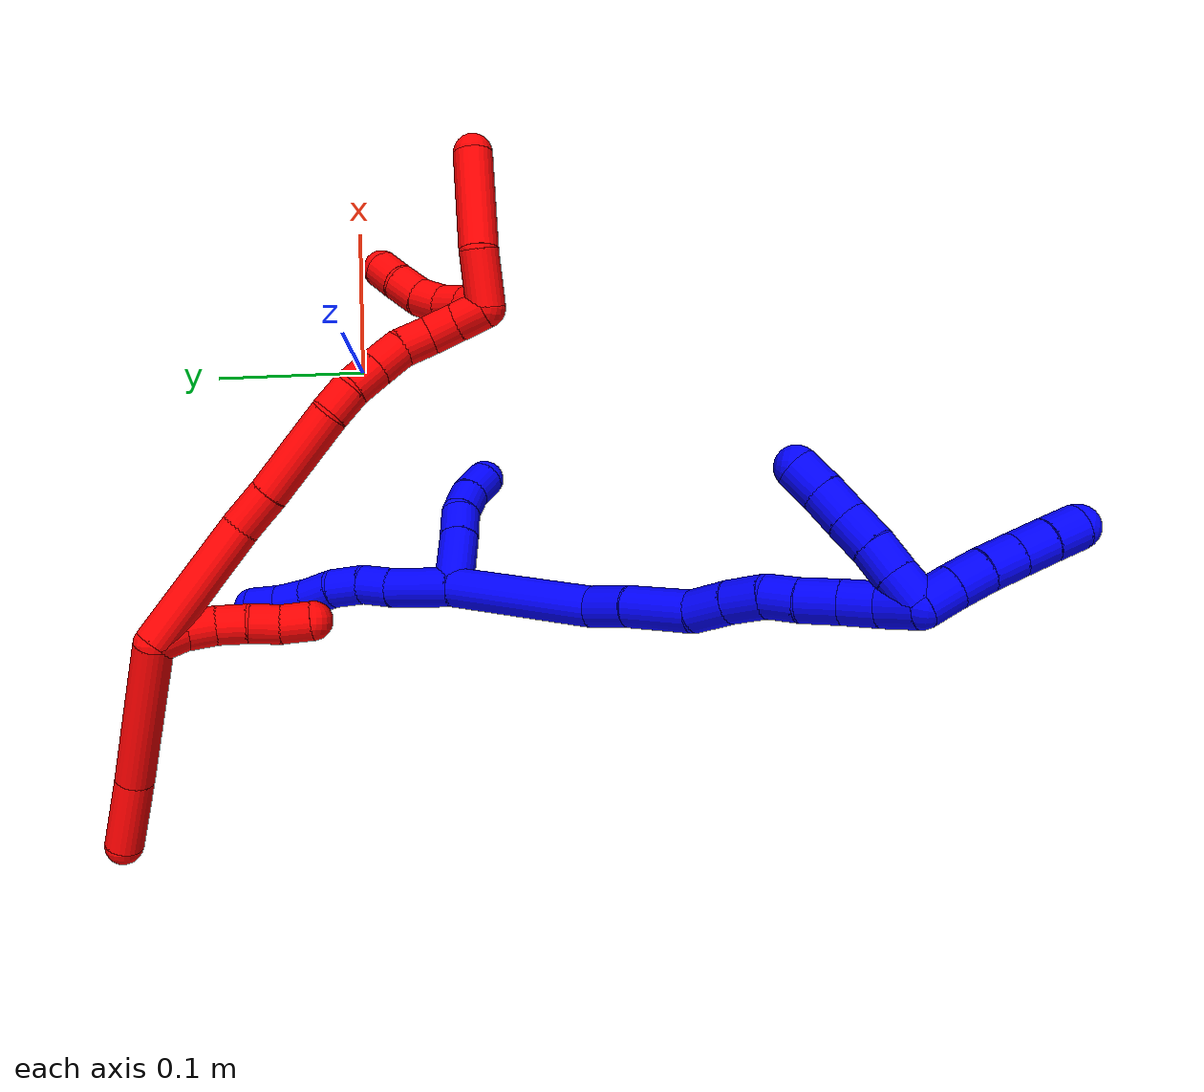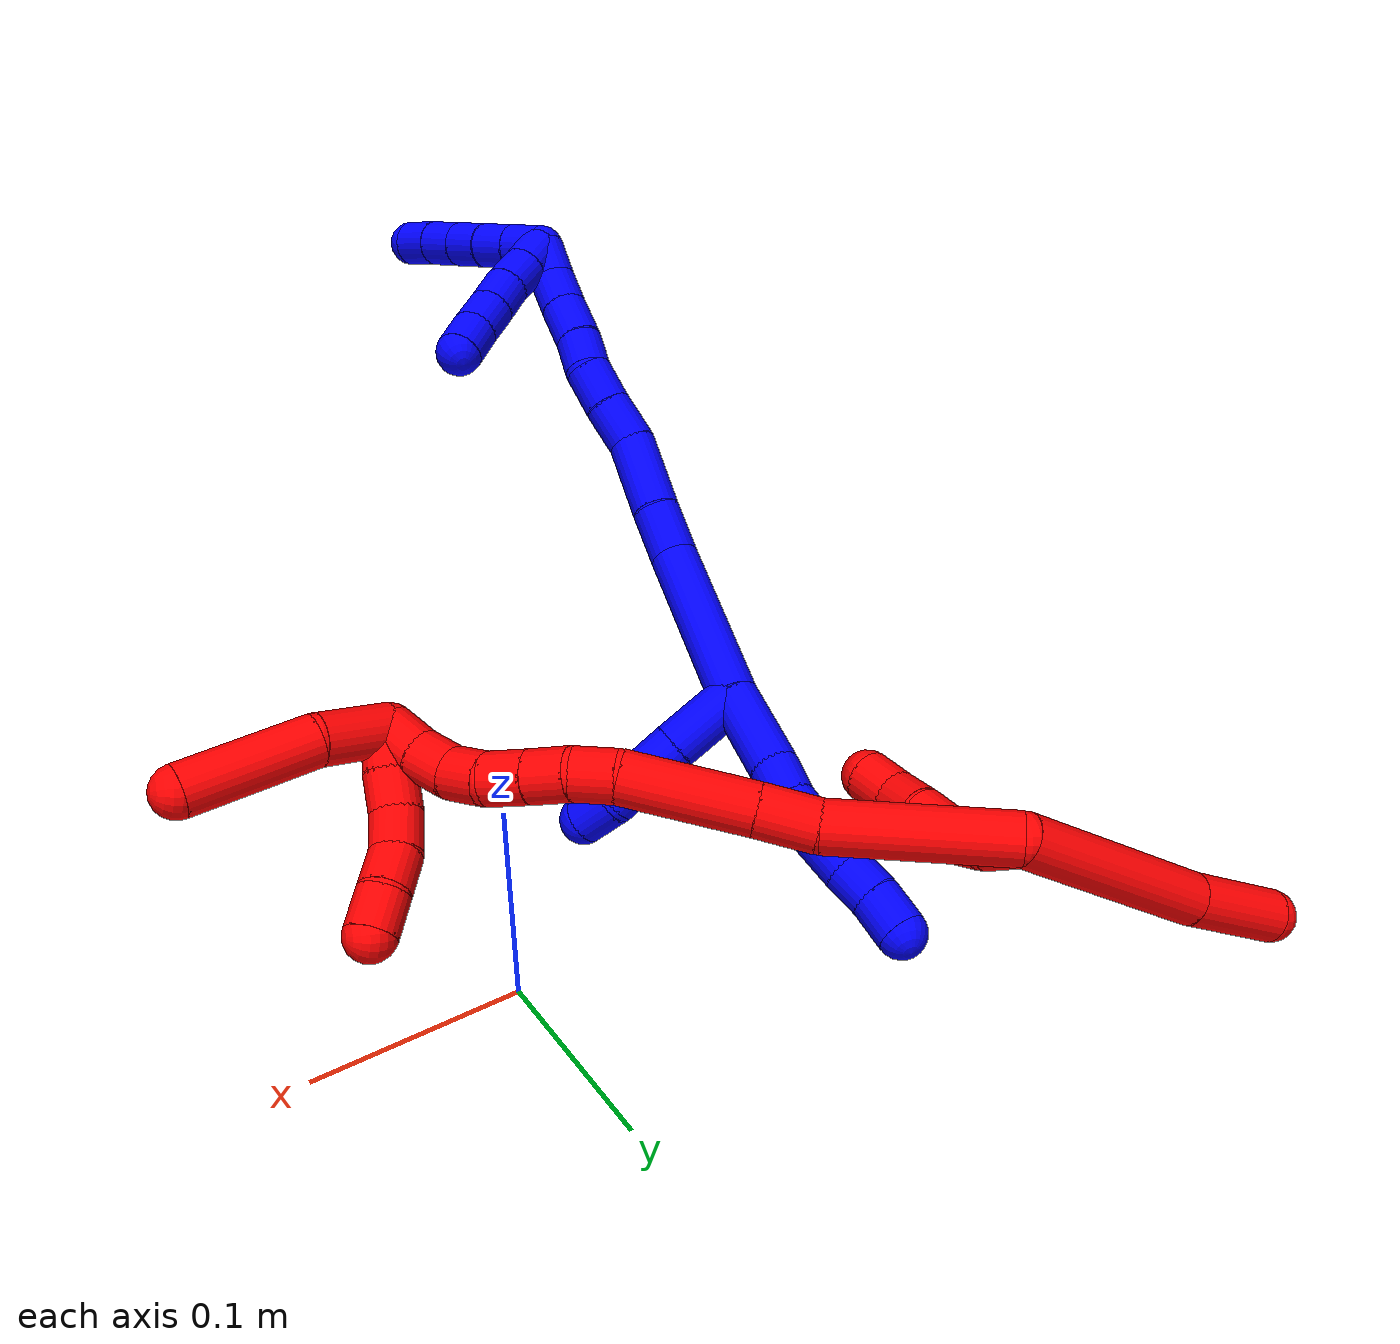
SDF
<sdf version="1.7">
 <world name="default">
  <plugin name="TubeGeneratorPlugin" filename="libtube_generator_plugin.so"/>
  <model name="photoneo_s_sensor">
   <static>1</static>
   <pose>0 0 2 1.57079 1.57079 3.14159</pose>
   <link name="link">
    <inertial><mass>0.1</mass></inertial>
    <sensor name="sensor" type="depth">
     <update_rate>30</update_rate>
     <camera>
      <horizontal_fov>1.22</horizontal_fov>
      <image><width>1920</width><height>1200</height><format>B8G8R8</format></image>
      <clip><near>0.1</near><far>4</far></clip>
      <depth_camera><output>points</output></depth_camera>
     </camera>
     <plugin name="camera_plugin" filename="libgazebo_ros_depth_camera.so">
      <baseline>0.2</baseline>
      <alwaysOn>1</alwaysOn>
      <updateRate>0.0</updateRate>
      <cameraName>camera_ir</cameraName>
      <imageTopicName>/camera/color/image_raw</imageTopicName>
      <cameraInfoTopicName>/camera/color/camera_info</cameraInfoTopicName>
      <depthImageTopicName>/camera/depth/image_raw</depthImageTopicName>
      <depthImageCameraInfoTopicName>/camera/depth/camera_info</depthImageCameraInfoTopicName>
      <pointCloudTopicName>/camera/depth/points</pointCloudTopicName>
      <frameName>fr_optical</frameName>
      <pointCloudCutoff>0.1</pointCloudCutoff>
      <pointCloudCutoffMax>2.0</pointCloudCutoffMax>
      <distortionK1>0</distortionK1>
      <distortionK2>0</distortionK2>
      <distortionK3>0</distortionK3>
      <distortionT1>0</distortionT1>
      <distortionT2>0</distortionT2>
      <CxPrime>0</CxPrime>
      <Cx>0</Cx>
      <Cy>0</Cy>
      <focalLength>0</focalLength>
      <hackBaseline>0</hackBaseline>
     </plugin>
    </sensor>
   </link>
  </model>
  <gravity>0 0 -9.8</gravity>
  <magnetic_field>6e-06 2.3e-05 -4.2e-05</magnetic_field>
  <atmosphere type="adiabatic"/>
  <physics name="default_physics" default="0" type="ode">
   <max_step_size>0.003</max_step_size>
   <real_time_factor>1</real_time_factor>
   <real_time_update_rate>1000</real_time_update_rate>
   <max_contacts>10000</max_contacts>
   <ode>
    <solver>
     <type>quick</type>
     <iters>100</iters>
     <sor>1.3</sor>
     <use_dynamic_moi_rescaling>0</use_dynamic_moi_rescaling>
    </solver>
    <constraints>
     <contact_max_correcting_vel>0</contact_max_correcting_vel>
     <contact_surface_layer>0.001</contact_surface_layer>
     <cfm>0</cfm>
     <erp>0.2</erp>
    </constraints>
   </ode>
  </physics>
  <scene><ambient>0.4 0.4 0.4 1</ambient><background>0.7 0.7 0.7 1</background><shadows>0</shadows></scene>
  <audio><device>default</device></audio>
  <spherical_coordinates>
   <surface_model>EARTH_WGS84</surface_model>
   <latitude_deg>0</latitude_deg>
   <longitude_deg>0</longitude_deg>
   <elevation>0</elevation>
   <heading_deg>0</heading_deg>
  </spherical_coordinates>
  <model name="bin">
   <static>1</static>
   <link name="bottom">
    <collision name="collision-bottom">
     <pose>0 0 -0.01 0 -0 0</pose>
     <geometry><box><size>0.8 0.6 0.02</size></box></geometry>
     <surface>
      <friction><ode><mu>100</mu><mu2>100</mu2></ode></friction>
      <contact><collide_bitmask>65535</collide_bitmask></contact>
     </surface>
    </collision>
   </link>
   <link name="west_wall">
    <collision name="collision-west_wall">
     <pose>-0.41 0 0.1 0 -0 0</pose>
     <geometry><box><size>0.02 0.6 0.2</size></box></geometry>
     <surface>
      <friction><ode><mu>100</mu><mu2>100</mu2></ode></friction>
      <contact><collide_bitmask>65535</collide_bitmask></contact>
     </surface>
    </collision>
   </link>
   <link name="east_wall">
    <collision name="collision-east_wall">
     <pose>0.41 0 0.1 0 -0 0</pose>
     <geometry><box><size>0.02 0.6 0.2</size></box></geometry>
     <surface>
      <friction><ode><mu>100</mu><mu2>100</mu2></ode></friction>
      <contact><collide_bitmask>65535</collide_bitmask></contact>
     </surface>
    </collision>
   </link>
   <link name="south_wall">
    <collision name="collision-south_wall">
     <pose>0 -0.31 0.1 0 -0 0</pose>
     <geometry><box><size>0.8 0.02 0.2</size></box></geometry>
     <surface>
      <friction><ode><mu>100</mu><mu2>100</mu2></ode></friction>
      <contact><collide_bitmask>65535</collide_bitmask></contact>
     </surface>
    </collision>
   </link>
   <link name="north_wall">
    <collision name="collision-north_wall">
     <pose>0 0.31 0.1 0 -0 0</pose>
     <geometry><box><size>0.8 0.02 0.2</size></box></geometry>
     <surface>
      <friction><ode><mu>100</mu><mu2>100</mu2></ode></friction>
      <contact><collide_bitmask>65535</collide_bitmask></contact>
     </surface>
    </collision>
   </link>
  </model>
  <model name="1">
   <static>0</static>
   <link name="1">
    <collision name="collision-cylinder-e_1_2_8">
     <pose>0.003681 0.00508 -0.021301 -2.90746 0.166554 -1.2345</pose>
     <geometry><cylinder><radius>0.0125</radius><length>0.04441</length></cylinder></geometry>
     <surface>
      <friction><ode><mu>1.16</mu><mu2>1.16</mu2><slip1>0</slip1><slip2>0</slip2></ode></friction>
      <contact><ode><kp>1e+06</kp><kd>1</kd><max_vel>0</max_vel><min_depth>0.001</min_depth></ode></contact>
     </surface>
    </collision>
    <visual name="visual-cylinder-e_1_2_8">
     <pose>0.003681 0.00508 -0.021301 -2.90746 0.166554 -1.2345</pose>
     <geometry><cylinder><radius>0.0125</radius><length>0.04441</length></cylinder></geometry>
     <material><ambient>0 0 1 1</ambient></material>
    </visual>
    <collision name="collision-cylinder-e_2_8_9">
     <pose>0.008081 0.011726 -0.052931 -2.99119 0.068609 -0.854826</pose>
     <geometry><cylinder><radius>0.0125</radius><length>0.020946</length></cylinder></geometry>
     <surface>
      <friction><ode><mu>1.16</mu><mu2>1.16</mu2><slip1>0</slip1><slip2>0</slip2></ode></friction>
      <contact><ode><kp>1e+06</kp><kd>1</kd><max_vel>0</max_vel><min_depth>0.001</min_depth></ode></contact>
     </surface>
    </collision>
    <visual name="visual-cylinder-e_2_8_9">
     <pose>0.008081 0.011726 -0.052931 -2.99119 0.068609 -0.854826</pose>
     <geometry><cylinder><radius>0.0125</radius><length>0.020946</length></cylinder></geometry>
     <material><ambient>0 0 1 1</ambient></material>
    </visual>
    <collision name="collision-cylinder-e_3_9_10">
     <pose>0.011891 0.015047 -0.073602 -2.97346 0.286702 -2.08474</pose>
     <geometry><cylinder><radius>0.0125</radius><length>0.021868</length></cylinder></geometry>
     <surface>
      <friction><ode><mu>1.16</mu><mu2>1.16</mu2><slip1>0</slip1><slip2>0</slip2></ode></friction>
      <contact><ode><kp>1e+06</kp><kd>1</kd><max_vel>0</max_vel><min_depth>0.001</min_depth></ode></contact>
     </surface>
    </collision>
    <visual name="visual-cylinder-e_3_9_10">
     <pose>0.011891 0.015047 -0.073602 -2.97346 0.286702 -2.08474</pose>
     <geometry><cylinder><radius>0.0125</radius><length>0.021868</length></cylinder></geometry>
     <material><ambient>0 0 1 1</ambient></material>
    </visual>
    <collision name="collision-cylinder-e_4_10_11">
     <pose>0.019364 0.020187 -0.093113 -2.78801 0.421343 -1.74963</pose>
     <geometry><cylinder><radius>0.0125</radius><length>0.021428</length></cylinder></geometry>
     <surface>
      <friction><ode><mu>1.16</mu><mu2>1.16</mu2><slip1>0</slip1><slip2>0</slip2></ode></friction>
      <contact><ode><kp>1e+06</kp><kd>1</kd><max_vel>0</max_vel><min_depth>0.001</min_depth></ode></contact>
     </surface>
    </collision>
    <visual name="visual-cylinder-e_4_10_11">
     <pose>0.019364 0.020187 -0.093113 -2.78801 0.421343 -1.74963</pose>
     <geometry><cylinder><radius>0.0125</radius><length>0.021428</length></cylinder></geometry>
     <material><ambient>0 0 1 1</ambient></material>
    </visual>
    <collision name="collision-cylinder-e_5_11_12">
     <pose>0.027533 0.024839 -0.11147 -3.00456 0.38774 -2.4691</pose>
     <geometry><cylinder><radius>0.0125</radius><length>0.020031</length></cylinder></geometry>
     <surface>
      <friction><ode><mu>1.16</mu><mu2>1.16</mu2><slip1>0</slip1><slip2>0</slip2></ode></friction>
      <contact><ode><kp>1e+06</kp><kd>1</kd><max_vel>0</max_vel><min_depth>0.001</min_depth></ode></contact>
     </surface>
    </collision>
    <visual name="visual-cylinder-e_5_11_12">
     <pose>0.027533 0.024839 -0.11147 -3.00456 0.38774 -2.4691</pose>
     <geometry><cylinder><radius>0.0125</radius><length>0.020031</length></cylinder></geometry>
     <material><ambient>0 0 1 1</ambient></material>
    </visual>
    <collision name="collision-cylinder-e_6_12_6">
     <pose>0.034039 0.027867 -0.13081 -2.96981 0.258001 -1.96963</pose>
     <geometry><cylinder><radius>0.0125</radius><length>0.021317</length></cylinder></geometry>
     <surface>
      <friction><ode><mu>1.16</mu><mu2>1.16</mu2><slip1>0</slip1><slip2>0</slip2></ode></friction>
      <contact><ode><kp>1e+06</kp><kd>1</kd><max_vel>0</max_vel><min_depth>0.001</min_depth></ode></contact>
     </surface>
    </collision>
    <visual name="visual-cylinder-e_6_12_6">
     <pose>0.034039 0.027867 -0.13081 -2.96981 0.258001 -1.96963</pose>
     <geometry><cylinder><radius>0.0125</radius><length>0.021317</length></cylinder></geometry>
     <material><ambient>0 0 1 1</ambient></material>
    </visual>
    <collision name="collision-cylinder-e_1_2_13">
     <pose>-0.016618 0.008636 -0.004537 -2.05456 -1.03994 1.51694</pose>
     <geometry><cylinder><radius>0.0125</radius><length>0.038539</length></cylinder></geometry>
     <surface>
      <friction><ode><mu>1.16</mu><mu2>1.16</mu2><slip1>0</slip1><slip2>0</slip2></ode></friction>
      <contact><ode><kp>1e+06</kp><kd>1</kd><max_vel>0</max_vel><min_depth>0.001</min_depth></ode></contact>
     </surface>
    </collision>
    <visual name="visual-cylinder-e_1_2_13">
     <pose>-0.016618 0.008636 -0.004537 -2.05456 -1.03994 1.51694</pose>
     <geometry><cylinder><radius>0.0125</radius><length>0.038539</length></cylinder></geometry>
     <material><ambient>0 0 1 1</ambient></material>
    </visual>
    <collision name="collision-cylinder-e_2_13_14">
     <pose>-0.041958 0.021716 -0.011844 -2.12807 -1.03017 1.59032</pose>
     <geometry><cylinder><radius>0.0125</radius><length>0.020348</length></cylinder></geometry>
     <surface>
      <friction><ode><mu>1.16</mu><mu2>1.16</mu2><slip1>0</slip1><slip2>0</slip2></ode></friction>
      <contact><ode><kp>1e+06</kp><kd>1</kd><max_vel>0</max_vel><min_depth>0.001</min_depth></ode></contact>
     </surface>
    </collision>
    <visual name="visual-cylinder-e_2_13_14">
     <pose>-0.041958 0.021716 -0.011844 -2.12807 -1.03017 1.59032</pose>
     <geometry><cylinder><radius>0.0125</radius><length>0.020348</length></cylinder></geometry>
     <material><ambient>0 0 1 1</ambient></material>
    </visual>
    <collision name="collision-cylinder-e_3_14_15">
     <pose>-0.058255 0.032805 -0.015215 -1.66105 -0.848614 0.918438</pose>
     <geometry><cylinder><radius>0.0125</radius><length>0.020187</length></cylinder></geometry>
     <surface>
      <friction><ode><mu>1.16</mu><mu2>1.16</mu2><slip1>0</slip1><slip2>0</slip2></ode></friction>
      <contact><ode><kp>1e+06</kp><kd>1</kd><max_vel>0</max_vel><min_depth>0.001</min_depth></ode></contact>
     </surface>
    </collision>
    <visual name="visual-cylinder-e_3_14_15">
     <pose>-0.058255 0.032805 -0.015215 -1.66105 -0.848614 0.918438</pose>
     <geometry><cylinder><radius>0.0125</radius><length>0.020187</length></cylinder></geometry>
     <material><ambient>0 0 1 1</ambient></material>
    </visual>
    <collision name="collision-cylinder-e_4_15_5">
     <pose>-0.073255 0.046581 -0.013952 -1.31506 -0.789191 0.622221</pose>
     <geometry><cylinder><radius>0.0125</radius><length>0.020926</length></cylinder></geometry>
     <surface>
      <friction><ode><mu>1.16</mu><mu2>1.16</mu2><slip1>0</slip1><slip2>0</slip2></ode></friction>
      <contact><ode><kp>1e+06</kp><kd>1</kd><max_vel>0</max_vel><min_depth>0.001</min_depth></ode></contact>
     </surface>
    </collision>
    <visual name="visual-cylinder-e_4_15_5">
     <pose>-0.073255 0.046581 -0.013952 -1.31506 -0.789191 0.622221</pose>
     <geometry><cylinder><radius>0.0125</radius><length>0.020926</length></cylinder></geometry>
     <material><ambient>0 0 1 1</ambient></material>
    </visual>
    <collision name="collision-cylinder-e_1_2_16">
     <pose>-0.001661 -0.008588 0.046033 0.18444 -0.035445 -0.003278</pose>
     <geometry><cylinder><radius>0.0125</radius><length>0.093714</length></cylinder></geometry>
     <surface>
      <friction><ode><mu>1.16</mu><mu2>1.16</mu2><slip1>0</slip1><slip2>0</slip2></ode></friction>
      <contact><ode><kp>1e+06</kp><kd>1</kd><max_vel>0</max_vel><min_depth>0.001</min_depth></ode></contact>
     </surface>
    </collision>
    <visual name="visual-cylinder-e_1_2_16">
     <pose>-0.001661 -0.008588 0.046033 0.18444 -0.035445 -0.003278</pose>
     <geometry><cylinder><radius>0.0125</radius><length>0.093714</length></cylinder></geometry>
     <material><ambient>0 0 1 1</ambient></material>
    </visual>
    <collision name="collision-cylinder-e_2_16_17">
     <pose>-0.004907 -0.023952 0.104396 0.50251 -0.112275 -0.028847</pose>
     <geometry><cylinder><radius>0.0125</radius><length>0.028316</length></cylinder></geometry>
     <surface>
      <friction><ode><mu>1.16</mu><mu2>1.16</mu2><slip1>0</slip1><slip2>0</slip2></ode></friction>
      <contact><ode><kp>1e+06</kp><kd>1</kd><max_vel>0</max_vel><min_depth>0.001</min_depth></ode></contact>
     </surface>
    </collision>
    <visual name="visual-cylinder-e_2_16_17">
     <pose>-0.004907 -0.023952 0.104396 0.50251 -0.112275 -0.028847</pose>
     <geometry><cylinder><radius>0.0125</radius><length>0.028316</length></cylinder></geometry>
     <material><ambient>0 0 1 1</ambient></material>
    </visual>
    <collision name="collision-cylinder-e_3_17_18">
     <pose>-0.007688 -0.039233 0.136179 0.412144 -0.056196 -0.01175</pose>
     <geometry><cylinder><radius>0.0125</radius><length>0.04253</length></cylinder></geometry>
     <surface>
      <friction><ode><mu>1.16</mu><mu2>1.16</mu2><slip1>0</slip1><slip2>0</slip2></ode></friction>
      <contact><ode><kp>1e+06</kp><kd>1</kd><max_vel>0</max_vel><min_depth>0.001</min_depth></ode></contact>
     </surface>
    </collision>
    <visual name="visual-cylinder-e_3_17_18">
     <pose>-0.007688 -0.039233 0.136179 0.412144 -0.056196 -0.01175</pose>
     <geometry><cylinder><radius>0.0125</radius><length>0.04253</length></cylinder></geometry>
     <material><ambient>0 0 1 1</ambient></material>
    </visual>
    <collision name="collision-cylinder-e_4_18_19">
     <pose>-0.012856 -0.053812 0.165922 0.533304 -0.321041 -0.088398</pose>
     <geometry><cylinder><radius>0.0125</radius><length>0.025183</length></cylinder></geometry>
     <surface>
      <friction><ode><mu>1.16</mu><mu2>1.16</mu2><slip1>0</slip1><slip2>0</slip2></ode></friction>
      <contact><ode><kp>1e+06</kp><kd>1</kd><max_vel>0</max_vel><min_depth>0.001</min_depth></ode></contact>
     </surface>
    </collision>
    <visual name="visual-cylinder-e_4_18_19">
     <pose>-0.012856 -0.053812 0.165922 0.533304 -0.321041 -0.088398</pose>
     <geometry><cylinder><radius>0.0125</radius><length>0.025183</length></cylinder></geometry>
     <material><ambient>0 0 1 1</ambient></material>
    </visual>
    <collision name="collision-cylinder-e_5_19_20">
     <pose>-0.019689 -0.065468 0.1862 0.509565 -0.244951 -0.064095</pose>
     <geometry><cylinder><radius>0.0125</radius><length>0.023591</length></cylinder></geometry>
     <surface>
      <friction><ode><mu>1.16</mu><mu2>1.16</mu2><slip1>0</slip1><slip2>0</slip2></ode></friction>
      <contact><ode><kp>1e+06</kp><kd>1</kd><max_vel>0</max_vel><min_depth>0.001</min_depth></ode></contact>
     </surface>
    </collision>
    <visual name="visual-cylinder-e_5_19_20">
     <pose>-0.019689 -0.065468 0.1862 0.509565 -0.244951 -0.064095</pose>
     <geometry><cylinder><radius>0.0125</radius><length>0.023591</length></cylinder></geometry>
     <material><ambient>0 0 1 1</ambient></material>
    </visual>
    <collision name="collision-cylinder-e_6_20_21">
     <pose>-0.022691 -0.074799 0.205484 0.383448 -0.01406 -0.002729</pose>
     <geometry><cylinder><radius>0.0125</radius><length>0.020046</length></cylinder></geometry>
     <surface>
      <friction><ode><mu>1.16</mu><mu2>1.16</mu2><slip1>0</slip1><slip2>0</slip2></ode></friction>
      <contact><ode><kp>1e+06</kp><kd>1</kd><max_vel>0</max_vel><min_depth>0.001</min_depth></ode></contact>
     </surface>
    </collision>
    <visual name="visual-cylinder-e_6_20_21">
     <pose>-0.022691 -0.074799 0.205484 0.383448 -0.01406 -0.002729</pose>
     <geometry><cylinder><radius>0.0125</radius><length>0.020046</length></cylinder></geometry>
     <material><ambient>0 0 1 1</ambient></material>
    </visual>
    <collision name="collision-cylinder-e_7_21_22">
     <pose>-0.024054 -0.082213 0.226015 0.315228 -0.103051 -0.016392</pose>
     <geometry><cylinder><radius>0.0125</radius><length>0.023763</length></cylinder></geometry>
     <surface>
      <friction><ode><mu>1.16</mu><mu2>1.16</mu2><slip1>0</slip1><slip2>0</slip2></ode></friction>
      <contact><ode><kp>1e+06</kp><kd>1</kd><max_vel>0</max_vel><min_depth>0.001</min_depth></ode></contact>
     </surface>
    </collision>
    <visual name="visual-cylinder-e_7_21_22">
     <pose>-0.024054 -0.082213 0.226015 0.315228 -0.103051 -0.016392</pose>
     <geometry><cylinder><radius>0.0125</radius><length>0.023763</length></cylinder></geometry>
     <material><ambient>0 0 1 1</ambient></material>
    </visual>
    <collision name="collision-cylinder-e_8_22_23">
     <pose>-0.026035 -0.089239 0.246994 0.332211 -0.073467 -0.012322</pose>
     <geometry><cylinder><radius>0.0125</radius><length>0.02067</length></cylinder></geometry>
     <surface>
      <friction><ode><mu>1.16</mu><mu2>1.16</mu2><slip1>0</slip1><slip2>0</slip2></ode></friction>
      <contact><ode><kp>1e+06</kp><kd>1</kd><max_vel>0</max_vel><min_depth>0.001</min_depth></ode></contact>
     </surface>
    </collision>
    <visual name="visual-cylinder-e_8_22_23">
     <pose>-0.026035 -0.089239 0.246994 0.332211 -0.073467 -0.012322</pose>
     <geometry><cylinder><radius>0.0125</radius><length>0.02067</length></cylinder></geometry>
     <material><ambient>0 0 1 1</ambient></material>
    </visual>
    <collision name="collision-cylinder-e_9_23_1">
     <pose>-0.027688 -0.097814 0.266489 0.491002 -0.080773 -0.020249</pose>
     <geometry><cylinder><radius>0.0125</radius><length>0.022187</length></cylinder></geometry>
     <surface>
      <friction><ode><mu>1.16</mu><mu2>1.16</mu2><slip1>0</slip1><slip2>0</slip2></ode></friction>
      <contact><ode><kp>1e+06</kp><kd>1</kd><max_vel>0</max_vel><min_depth>0.001</min_depth></ode></contact>
     </surface>
    </collision>
    <visual name="visual-cylinder-e_9_23_1">
     <pose>-0.027688 -0.097814 0.266489 0.491002 -0.080773 -0.020249</pose>
     <geometry><cylinder><radius>0.0125</radius><length>0.022187</length></cylinder></geometry>
     <material><ambient>0 0 1 1</ambient></material>
    </visual>
    <collision name="collision-cylinder-e_1_1_24">
     <pose>-0.035219 -0.101799 0.26886 -2.97668 -0.72554 2.71283</pose>
     <geometry><cylinder><radius>0.0125</radius><length>0.02</length></cylinder></geometry>
     <surface>
      <friction><ode><mu>1.16</mu><mu2>1.16</mu2><slip1>0</slip1><slip2>0</slip2></ode></friction>
      <contact><ode><kp>1e+06</kp><kd>1</kd><max_vel>0</max_vel><min_depth>0.001</min_depth></ode></contact>
     </surface>
    </collision>
    <visual name="visual-cylinder-e_1_1_24">
     <pose>-0.035219 -0.101799 0.26886 -2.97668 -0.72554 2.71283</pose>
     <geometry><cylinder><radius>0.0125</radius><length>0.02</length></cylinder></geometry>
     <material><ambient>0 0 1 1</ambient></material>
    </visual>
    <collision name="collision-cylinder-e_2_24_25">
     <pose>-0.048711 -0.099496 0.254281 -2.99334 -0.75556 2.77161</pose>
     <geometry><cylinder><radius>0.0125</radius><length>0.02</length></cylinder></geometry>
     <surface>
      <friction><ode><mu>1.16</mu><mu2>1.16</mu2><slip1>0</slip1><slip2>0</slip2></ode></friction>
      <contact><ode><kp>1e+06</kp><kd>1</kd><max_vel>0</max_vel><min_depth>0.001</min_depth></ode></contact>
     </surface>
    </collision>
    <visual name="visual-cylinder-e_2_24_25">
     <pose>-0.048711 -0.099496 0.254281 -2.99334 -0.75556 2.77161</pose>
     <geometry><cylinder><radius>0.0125</radius><length>0.02</length></cylinder></geometry>
     <material><ambient>0 0 1 1</ambient></material>
    </visual>
    <collision name="collision-cylinder-e_3_25_26">
     <pose>-0.061698 -0.097096 0.239293 -2.97312 -0.659879 2.65813</pose>
     <geometry><cylinder><radius>0.0125</radius><length>0.02</length></cylinder></geometry>
     <surface>
      <friction><ode><mu>1.16</mu><mu2>1.16</mu2><slip1>0</slip1><slip2>0</slip2></ode></friction>
      <contact><ode><kp>1e+06</kp><kd>1</kd><max_vel>0</max_vel><min_depth>0.001</min_depth></ode></contact>
     </surface>
    </collision>
    <visual name="visual-cylinder-e_3_25_26">
     <pose>-0.061698 -0.097096 0.239293 -2.97312 -0.659879 2.65813</pose>
     <geometry><cylinder><radius>0.0125</radius><length>0.02</length></cylinder></geometry>
     <material><ambient>0 0 1 1</ambient></material>
    </visual>
    <collision name="collision-cylinder-e_4_26_27">
     <pose>-0.074087 -0.094616 0.223791 -2.99295 -0.676144 2.7242</pose>
     <geometry><cylinder><radius>0.0125</radius><length>0.02</length></cylinder></geometry>
     <surface>
      <friction><ode><mu>1.16</mu><mu2>1.16</mu2><slip1>0</slip1><slip2>0</slip2></ode></friction>
      <contact><ode><kp>1e+06</kp><kd>1</kd><max_vel>0</max_vel><min_depth>0.001</min_depth></ode></contact>
     </surface>
    </collision>
    <visual name="visual-cylinder-e_4_26_27">
     <pose>-0.074087 -0.094616 0.223791 -2.99295 -0.676144 2.7242</pose>
     <geometry><cylinder><radius>0.0125</radius><length>0.02</length></cylinder></geometry>
     <material><ambient>0 0 1 1</ambient></material>
    </visual>
    <collision name="collision-cylinder-e_5_27_4">
     <pose>-0.086154 -0.092538 0.20799 -3.02795 -0.619883 2.79003</pose>
     <geometry><cylinder><radius>0.0125</radius><length>0.02</length></cylinder></geometry>
     <surface>
      <friction><ode><mu>1.16</mu><mu2>1.16</mu2><slip1>0</slip1><slip2>0</slip2></ode></friction>
      <contact><ode><kp>1e+06</kp><kd>1</kd><max_vel>0</max_vel><min_depth>0.001</min_depth></ode></contact>
     </surface>
    </collision>
    <visual name="visual-cylinder-e_5_27_4">
     <pose>-0.086154 -0.092538 0.20799 -3.02795 -0.619883 2.79003</pose>
     <geometry><cylinder><radius>0.0125</radius><length>0.02</length></cylinder></geometry>
     <material><ambient>0 0 1 1</ambient></material>
    </visual>
    <collision name="collision-cylinder-e_1_1_28">
     <pose>-0.035277 -0.100344 0.283168 -0.369594 -0.733268 0.143315</pose>
     <geometry><cylinder><radius>0.0125</radius><length>0.02</length></cylinder></geometry>
     <surface>
      <friction><ode><mu>1.16</mu><mu2>1.16</mu2><slip1>0</slip1><slip2>0</slip2></ode></friction>
      <contact><ode><kp>1e+06</kp><kd>1</kd><max_vel>0</max_vel><min_depth>0.001</min_depth></ode></contact>
     </surface>
    </collision>
    <visual name="visual-cylinder-e_1_1_28">
     <pose>-0.035277 -0.100344 0.283168 -0.369594 -0.733268 0.143315</pose>
     <geometry><cylinder><radius>0.0125</radius><length>0.02</length></cylinder></geometry>
     <material><ambient>0 0 1 1</ambient></material>
    </visual>
    <collision name="collision-cylinder-e_2_28_29">
     <pose>-0.048419 -0.094971 0.29725 -0.359495 -0.700984 0.132666</pose>
     <geometry><cylinder><radius>0.0125</radius><length>0.02</length></cylinder></geometry>
     <surface>
      <friction><ode><mu>1.16</mu><mu2>1.16</mu2><slip1>0</slip1><slip2>0</slip2></ode></friction>
      <contact><ode><kp>1e+06</kp><kd>1</kd><max_vel>0</max_vel><min_depth>0.001</min_depth></ode></contact>
     </surface>
    </collision>
    <visual name="visual-cylinder-e_2_28_29">
     <pose>-0.048419 -0.094971 0.29725 -0.359495 -0.700984 0.132666</pose>
     <geometry><cylinder><radius>0.0125</radius><length>0.02</length></cylinder></geometry>
     <material><ambient>0 0 1 1</ambient></material>
    </visual>
    <collision name="collision-cylinder-e_3_29_30">
     <pose>-0.060831 -0.089234 0.31183 -0.389484 -0.638816 0.130284</pose>
     <geometry><cylinder><radius>0.0125</radius><length>0.02</length></cylinder></geometry>
     <surface>
      <friction><ode><mu>1.16</mu><mu2>1.16</mu2><slip1>0</slip1><slip2>0</slip2></ode></friction>
      <contact><ode><kp>1e+06</kp><kd>1</kd><max_vel>0</max_vel><min_depth>0.001</min_depth></ode></contact>
     </surface>
    </collision>
    <visual name="visual-cylinder-e_3_29_30">
     <pose>-0.060831 -0.089234 0.31183 -0.389484 -0.638816 0.130284</pose>
     <geometry><cylinder><radius>0.0125</radius><length>0.02</length></cylinder></geometry>
     <material><ambient>0 0 1 1</ambient></material>
    </visual>
    <collision name="collision-cylinder-e_4_30_31">
     <pose>-0.072741 -0.083195 0.326719 -0.381174 -0.636971 0.12705</pose>
     <geometry><cylinder><radius>0.0125</radius><length>0.02</length></cylinder></geometry>
     <surface>
      <friction><ode><mu>1.16</mu><mu2>1.16</mu2><slip1>0</slip1><slip2>0</slip2></ode></friction>
      <contact><ode><kp>1e+06</kp><kd>1</kd><max_vel>0</max_vel><min_depth>0.001</min_depth></ode></contact>
     </surface>
    </collision>
    <visual name="visual-cylinder-e_4_30_31">
     <pose>-0.072741 -0.083195 0.326719 -0.381174 -0.636971 0.12705</pose>
     <geometry><cylinder><radius>0.0125</radius><length>0.02</length></cylinder></geometry>
     <material><ambient>0 0 1 1</ambient></material>
    </visual>
    <collision name="collision-cylinder-e_5_31_3">
     <pose>-0.084499 -0.076724 0.341538 -0.44189 -0.619987 0.143648</pose>
     <geometry><cylinder><radius>0.0125</radius><length>0.02</length></cylinder></geometry>
     <surface>
      <friction><ode><mu>1.16</mu><mu2>1.16</mu2><slip1>0</slip1><slip2>0</slip2></ode></friction>
      <contact><ode><kp>1e+06</kp><kd>1</kd><max_vel>0</max_vel><min_depth>0.001</min_depth></ode></contact>
     </surface>
    </collision>
    <visual name="visual-cylinder-e_5_31_3">
     <pose>-0.084499 -0.076724 0.341538 -0.44189 -0.619987 0.143648</pose>
     <geometry><cylinder><radius>0.0125</radius><length>0.02</length></cylinder></geometry>
     <material><ambient>0 0 1 1</ambient></material>
    </visual>
    <collision name="collision-sphere-3">
     <pose>-0.09031 -0.073244 0.348895 0 -0 0</pose>
     <geometry><sphere><radius>0.0125</radius></sphere></geometry>
     <surface>
      <friction><ode><mu>1.16</mu><mu2>1.16</mu2><slip1>0</slip1><slip2>0</slip2></ode></friction>
      <contact><ode><kp>1e+06</kp><kd>1</kd><max_vel>0</max_vel><min_depth>0.001</min_depth></ode></contact>
     </surface>
    </collision>
    <visual name="visual-sphere-3">
     <pose>-0.09031 -0.073244 0.348895 0 -0 0</pose>
     <geometry><sphere><radius>0.0125</radius></sphere></geometry>
     <material><ambient>0 0 1 1</ambient></material>
    </visual>
    <collision name="collision-sphere-31">
     <pose>-0.078689 -0.080205 0.334181 0 -0 0</pose>
     <geometry><sphere><radius>0.0125</radius></sphere></geometry>
     <surface>
      <friction><ode><mu>1.16</mu><mu2>1.16</mu2><slip1>0</slip1><slip2>0</slip2></ode></friction>
      <contact><ode><kp>1e+06</kp><kd>1</kd><max_vel>0</max_vel><min_depth>0.001</min_depth></ode></contact>
     </surface>
    </collision>
    <visual name="visual-sphere-31">
     <pose>-0.078689 -0.080205 0.334181 0 -0 0</pose>
     <geometry><sphere><radius>0.0125</radius></sphere></geometry>
     <material><ambient>0 0 1 1</ambient></material>
    </visual>
    <collision name="collision-sphere-30">
     <pose>-0.066794 -0.086186 0.319257 0 -0 0</pose>
     <geometry><sphere><radius>0.0125</radius></sphere></geometry>
     <surface>
      <friction><ode><mu>1.16</mu><mu2>1.16</mu2><slip1>0</slip1><slip2>0</slip2></ode></friction>
      <contact><ode><kp>1e+06</kp><kd>1</kd><max_vel>0</max_vel><min_depth>0.001</min_depth></ode></contact>
     </surface>
    </collision>
    <visual name="visual-sphere-30">
     <pose>-0.066794 -0.086186 0.319257 0 -0 0</pose>
     <geometry><sphere><radius>0.0125</radius></sphere></geometry>
     <material><ambient>0 0 1 1</ambient></material>
    </visual>
    <collision name="collision-sphere-29">
     <pose>-0.054869 -0.092283 0.304404 0 -0 0</pose>
     <geometry><sphere><radius>0.0125</radius></sphere></geometry>
     <surface>
      <friction><ode><mu>1.16</mu><mu2>1.16</mu2><slip1>0</slip1><slip2>0</slip2></ode></friction>
      <contact><ode><kp>1e+06</kp><kd>1</kd><max_vel>0</max_vel><min_depth>0.001</min_depth></ode></contact>
     </surface>
    </collision>
    <visual name="visual-sphere-29">
     <pose>-0.054869 -0.092283 0.304404 0 -0 0</pose>
     <geometry><sphere><radius>0.0125</radius></sphere></geometry>
     <material><ambient>0 0 1 1</ambient></material>
    </visual>
    <collision name="collision-sphere-28">
     <pose>-0.04197 -0.09766 0.290096 0 -0 0</pose>
     <geometry><sphere><radius>0.0125</radius></sphere></geometry>
     <surface>
      <friction><ode><mu>1.16</mu><mu2>1.16</mu2><slip1>0</slip1><slip2>0</slip2></ode></friction>
      <contact><ode><kp>1e+06</kp><kd>1</kd><max_vel>0</max_vel><min_depth>0.001</min_depth></ode></contact>
     </surface>
    </collision>
    <visual name="visual-sphere-28">
     <pose>-0.04197 -0.09766 0.290096 0 -0 0</pose>
     <geometry><sphere><radius>0.0125</radius></sphere></geometry>
     <material><ambient>0 0 1 1</ambient></material>
    </visual>
    <collision name="collision-sphere-4">
     <pose>-0.091963 -0.091615 0.199903 0 -0 0</pose>
     <geometry><sphere><radius>0.0125</radius></sphere></geometry>
     <surface>
      <friction><ode><mu>1.16</mu><mu2>1.16</mu2><slip1>0</slip1><slip2>0</slip2></ode></friction>
      <contact><ode><kp>1e+06</kp><kd>1</kd><max_vel>0</max_vel><min_depth>0.001</min_depth></ode></contact>
     </surface>
    </collision>
    <visual name="visual-sphere-4">
     <pose>-0.091963 -0.091615 0.199903 0 -0 0</pose>
     <geometry><sphere><radius>0.0125</radius></sphere></geometry>
     <material><ambient>0 0 1 1</ambient></material>
    </visual>
    <collision name="collision-sphere-27">
     <pose>-0.080344 -0.093461 0.216077 0 -0 0</pose>
     <geometry><sphere><radius>0.0125</radius></sphere></geometry>
     <surface>
      <friction><ode><mu>1.16</mu><mu2>1.16</mu2><slip1>0</slip1><slip2>0</slip2></ode></friction>
      <contact><ode><kp>1e+06</kp><kd>1</kd><max_vel>0</max_vel><min_depth>0.001</min_depth></ode></contact>
     </surface>
    </collision>
    <visual name="visual-sphere-27">
     <pose>-0.080344 -0.093461 0.216077 0 -0 0</pose>
     <geometry><sphere><radius>0.0125</radius></sphere></geometry>
     <material><ambient>0 0 1 1</ambient></material>
    </visual>
    <collision name="collision-sphere-26">
     <pose>-0.067829 -0.095771 0.231504 0 -0 0</pose>
     <geometry><sphere><radius>0.0125</radius></sphere></geometry>
     <surface>
      <friction><ode><mu>1.16</mu><mu2>1.16</mu2><slip1>0</slip1><slip2>0</slip2></ode></friction>
      <contact><ode><kp>1e+06</kp><kd>1</kd><max_vel>0</max_vel><min_depth>0.001</min_depth></ode></contact>
     </surface>
    </collision>
    <visual name="visual-sphere-26">
     <pose>-0.067829 -0.095771 0.231504 0 -0 0</pose>
     <geometry><sphere><radius>0.0125</radius></sphere></geometry>
     <material><ambient>0 0 1 1</ambient></material>
    </visual>
    <collision name="collision-sphere-25">
     <pose>-0.055568 -0.098421 0.247082 0 -0 0</pose>
     <geometry><sphere><radius>0.0125</radius></sphere></geometry>
     <surface>
      <friction><ode><mu>1.16</mu><mu2>1.16</mu2><slip1>0</slip1><slip2>0</slip2></ode></friction>
      <contact><ode><kp>1e+06</kp><kd>1</kd><max_vel>0</max_vel><min_depth>0.001</min_depth></ode></contact>
     </surface>
    </collision>
    <visual name="visual-sphere-25">
     <pose>-0.055568 -0.098421 0.247082 0 -0 0</pose>
     <geometry><sphere><radius>0.0125</radius></sphere></geometry>
     <material><ambient>0 0 1 1</ambient></material>
    </visual>
    <collision name="collision-sphere-24">
     <pose>-0.041854 -0.100571 0.26148 0 -0 0</pose>
     <geometry><sphere><radius>0.0125</radius></sphere></geometry>
     <surface>
      <friction><ode><mu>1.16</mu><mu2>1.16</mu2><slip1>0</slip1><slip2>0</slip2></ode></friction>
      <contact><ode><kp>1e+06</kp><kd>1</kd><max_vel>0</max_vel><min_depth>0.001</min_depth></ode></contact>
     </surface>
    </collision>
    <visual name="visual-sphere-24">
     <pose>-0.041854 -0.100571 0.26148 0 -0 0</pose>
     <geometry><sphere><radius>0.0125</radius></sphere></geometry>
     <material><ambient>0 0 1 1</ambient></material>
    </visual>
    <collision name="collision-sphere-1">
     <pose>-0.028583 -0.103027 0.27624 0 -0 0</pose>
     <geometry><sphere><radius>0.0125</radius></sphere></geometry>
     <surface>
      <friction><ode><mu>1.16</mu><mu2>1.16</mu2><slip1>0</slip1><slip2>0</slip2></ode></friction>
      <contact><ode><kp>1e+06</kp><kd>1</kd><max_vel>0</max_vel><min_depth>0.001</min_depth></ode></contact>
     </surface>
    </collision>
    <visual name="visual-sphere-1">
     <pose>-0.028583 -0.103027 0.27624 0 -0 0</pose>
     <geometry><sphere><radius>0.0125</radius></sphere></geometry>
     <material><ambient>0 0 1 1</ambient></material>
    </visual>
    <collision name="collision-sphere-23">
     <pose>-0.026793 -0.0926 0.256738 0 -0 0</pose>
     <geometry><sphere><radius>0.0125</radius></sphere></geometry>
     <surface>
      <friction><ode><mu>1.16</mu><mu2>1.16</mu2><slip1>0</slip1><slip2>0</slip2></ode></friction>
      <contact><ode><kp>1e+06</kp><kd>1</kd><max_vel>0</max_vel><min_depth>0.001</min_depth></ode></contact>
     </surface>
    </collision>
    <visual name="visual-sphere-23">
     <pose>-0.026793 -0.0926 0.256738 0 -0 0</pose>
     <geometry><sphere><radius>0.0125</radius></sphere></geometry>
     <material><ambient>0 0 1 1</ambient></material>
    </visual>
    <collision name="collision-sphere-22">
     <pose>-0.025276 -0.085877 0.237251 0 -0 0</pose>
     <geometry><sphere><radius>0.0125</radius></sphere></geometry>
     <surface>
      <friction><ode><mu>1.16</mu><mu2>1.16</mu2><slip1>0</slip1><slip2>0</slip2></ode></friction>
      <contact><ode><kp>1e+06</kp><kd>1</kd><max_vel>0</max_vel><min_depth>0.001</min_depth></ode></contact>
     </surface>
    </collision>
    <visual name="visual-sphere-22">
     <pose>-0.025276 -0.085877 0.237251 0 -0 0</pose>
     <geometry><sphere><radius>0.0125</radius></sphere></geometry>
     <material><ambient>0 0 1 1</ambient></material>
    </visual>
    <collision name="collision-sphere-21">
     <pose>-0.022832 -0.078549 0.214778 0 -0 0</pose>
     <geometry><sphere><radius>0.0125</radius></sphere></geometry>
     <surface>
      <friction><ode><mu>1.16</mu><mu2>1.16</mu2><slip1>0</slip1><slip2>0</slip2></ode></friction>
      <contact><ode><kp>1e+06</kp><kd>1</kd><max_vel>0</max_vel><min_depth>0.001</min_depth></ode></contact>
     </surface>
    </collision>
    <visual name="visual-sphere-21">
     <pose>-0.022832 -0.078549 0.214778 0 -0 0</pose>
     <geometry><sphere><radius>0.0125</radius></sphere></geometry>
     <material><ambient>0 0 1 1</ambient></material>
    </visual>
    <collision name="collision-sphere-12">
     <pose>0.03132 0.026105 -0.120656 0 -0 0</pose>
     <geometry><sphere><radius>0.0125</radius></sphere></geometry>
     <surface>
      <friction><ode><mu>1.16</mu><mu2>1.16</mu2><slip1>0</slip1><slip2>0</slip2></ode></friction>
      <contact><ode><kp>1e+06</kp><kd>1</kd><max_vel>0</max_vel><min_depth>0.001</min_depth></ode></contact>
     </surface>
    </collision>
    <visual name="visual-sphere-12">
     <pose>0.03132 0.026105 -0.120656 0 -0 0</pose>
     <geometry><sphere><radius>0.0125</radius></sphere></geometry>
     <material><ambient>0 0 1 1</ambient></material>
    </visual>
    <collision name="collision-sphere-11">
     <pose>0.023746 0.023572 -0.102285 0 -0 0</pose>
     <geometry><sphere><radius>0.0125</radius></sphere></geometry>
     <surface>
      <friction><ode><mu>1.16</mu><mu2>1.16</mu2><slip1>0</slip1><slip2>0</slip2></ode></friction>
      <contact><ode><kp>1e+06</kp><kd>1</kd><max_vel>0</max_vel><min_depth>0.001</min_depth></ode></contact>
     </surface>
    </collision>
    <visual name="visual-sphere-11">
     <pose>0.023746 0.023572 -0.102285 0 -0 0</pose>
     <geometry><sphere><radius>0.0125</radius></sphere></geometry>
     <material><ambient>0 0 1 1</ambient></material>
    </visual>
    <collision name="collision-sphere-10">
     <pose>0.014983 0.016802 -0.083941 0 -0 0</pose>
     <geometry><sphere><radius>0.0125</radius></sphere></geometry>
     <surface>
      <friction><ode><mu>1.16</mu><mu2>1.16</mu2><slip1>0</slip1><slip2>0</slip2></ode></friction>
      <contact><ode><kp>1e+06</kp><kd>1</kd><max_vel>0</max_vel><min_depth>0.001</min_depth></ode></contact>
     </surface>
    </collision>
    <visual name="visual-sphere-10">
     <pose>0.014983 0.016802 -0.083941 0 -0 0</pose>
     <geometry><sphere><radius>0.0125</radius></sphere></geometry>
     <material><ambient>0 0 1 1</ambient></material>
    </visual>
    <collision name="collision-sphere-9">
     <pose>0.008799 0.013291 -0.063262 0 -0 0</pose>
     <geometry><sphere><radius>0.0125</radius></sphere></geometry>
     <surface>
      <friction><ode><mu>1.16</mu><mu2>1.16</mu2><slip1>0</slip1><slip2>0</slip2></ode></friction>
      <contact><ode><kp>1e+06</kp><kd>1</kd><max_vel>0</max_vel><min_depth>0.001</min_depth></ode></contact>
     </surface>
    </collision>
    <visual name="visual-sphere-9">
     <pose>0.008799 0.013291 -0.063262 0 -0 0</pose>
     <geometry><sphere><radius>0.0125</radius></sphere></geometry>
     <material><ambient>0 0 1 1</ambient></material>
    </visual>
    <collision name="collision-sphere-2">
     <geometry><sphere><radius>0.0125</radius></sphere></geometry>
     <surface>
      <friction><ode><mu>1.16</mu><mu2>1.16</mu2><slip1>0</slip1><slip2>0</slip2></ode></friction>
      <contact><ode><kp>1e+06</kp><kd>1</kd><max_vel>0</max_vel><min_depth>0.001</min_depth></ode></contact>
     </surface>
    </collision>
    <visual name="visual-sphere-2">
     <geometry><sphere><radius>0.0125</radius></sphere></geometry>
     <material><ambient>0 0 1 1</ambient></material>
    </visual>
    <collision name="collision-sphere-19">
     <pose>-0.016829 -0.059886 0.176211 0 -0 0</pose>
     <geometry><sphere><radius>0.0125</radius></sphere></geometry>
     <surface>
      <friction><ode><mu>1.16</mu><mu2>1.16</mu2><slip1>0</slip1><slip2>0</slip2></ode></friction>
      <contact><ode><kp>1e+06</kp><kd>1</kd><max_vel>0</max_vel><min_depth>0.001</min_depth></ode></contact>
     </surface>
    </collision>
    <visual name="visual-sphere-19">
     <pose>-0.016829 -0.059886 0.176211 0 -0 0</pose>
     <geometry><sphere><radius>0.0125</radius></sphere></geometry>
     <material><ambient>0 0 1 1</ambient></material>
    </visual>
    <collision name="collision-sphere-8">
     <pose>0.007363 0.01016 -0.042601 0 -0 0</pose>
     <geometry><sphere><radius>0.0125</radius></sphere></geometry>
     <surface>
      <friction><ode><mu>1.16</mu><mu2>1.16</mu2><slip1>0</slip1><slip2>0</slip2></ode></friction>
      <contact><ode><kp>1e+06</kp><kd>1</kd><max_vel>0</max_vel><min_depth>0.001</min_depth></ode></contact>
     </surface>
    </collision>
    <visual name="visual-sphere-8">
     <pose>0.007363 0.01016 -0.042601 0 -0 0</pose>
     <geometry><sphere><radius>0.0125</radius></sphere></geometry>
     <material><ambient>0 0 1 1</ambient></material>
    </visual>
    <collision name="collision-sphere-6">
     <pose>0.036759 0.029629 -0.140964 0 -0 0</pose>
     <geometry><sphere><radius>0.0125</radius></sphere></geometry>
     <surface>
      <friction><ode><mu>1.16</mu><mu2>1.16</mu2><slip1>0</slip1><slip2>0</slip2></ode></friction>
      <contact><ode><kp>1e+06</kp><kd>1</kd><max_vel>0</max_vel><min_depth>0.001</min_depth></ode></contact>
     </surface>
    </collision>
    <visual name="visual-sphere-6">
     <pose>0.036759 0.029629 -0.140964 0 -0 0</pose>
     <geometry><sphere><radius>0.0125</radius></sphere></geometry>
     <material><ambient>0 0 1 1</ambient></material>
    </visual>
    <collision name="collision-sphere-13">
     <pose>-0.033235 0.017272 -0.009075 0 -0 0</pose>
     <geometry><sphere><radius>0.0125</radius></sphere></geometry>
     <surface>
      <friction><ode><mu>1.16</mu><mu2>1.16</mu2><slip1>0</slip1><slip2>0</slip2></ode></friction>
      <contact><ode><kp>1e+06</kp><kd>1</kd><max_vel>0</max_vel><min_depth>0.001</min_depth></ode></contact>
     </surface>
    </collision>
    <visual name="visual-sphere-13">
     <pose>-0.033235 0.017272 -0.009075 0 -0 0</pose>
     <geometry><sphere><radius>0.0125</radius></sphere></geometry>
     <material><ambient>0 0 1 1</ambient></material>
    </visual>
    <collision name="collision-sphere-14">
     <pose>-0.050682 0.02616 -0.014614 0 -0 0</pose>
     <geometry><sphere><radius>0.0125</radius></sphere></geometry>
     <surface>
      <friction><ode><mu>1.16</mu><mu2>1.16</mu2><slip1>0</slip1><slip2>0</slip2></ode></friction>
      <contact><ode><kp>1e+06</kp><kd>1</kd><max_vel>0</max_vel><min_depth>0.001</min_depth></ode></contact>
     </surface>
    </collision>
    <visual name="visual-sphere-14">
     <pose>-0.050682 0.02616 -0.014614 0 -0 0</pose>
     <geometry><sphere><radius>0.0125</radius></sphere></geometry>
     <material><ambient>0 0 1 1</ambient></material>
    </visual>
    <collision name="collision-sphere-15">
     <pose>-0.065829 0.03945 -0.015816 0 -0 0</pose>
     <geometry><sphere><radius>0.0125</radius></sphere></geometry>
     <surface>
      <friction><ode><mu>1.16</mu><mu2>1.16</mu2><slip1>0</slip1><slip2>0</slip2></ode></friction>
      <contact><ode><kp>1e+06</kp><kd>1</kd><max_vel>0</max_vel><min_depth>0.001</min_depth></ode></contact>
     </surface>
    </collision>
    <visual name="visual-sphere-15">
     <pose>-0.065829 0.03945 -0.015816 0 -0 0</pose>
     <geometry><sphere><radius>0.0125</radius></sphere></geometry>
     <material><ambient>0 0 1 1</ambient></material>
    </visual>
    <collision name="collision-sphere-5">
     <pose>-0.080682 0.053711 -0.012088 0 -0 0</pose>
     <geometry><sphere><radius>0.0125</radius></sphere></geometry>
     <surface>
      <friction><ode><mu>1.16</mu><mu2>1.16</mu2><slip1>0</slip1><slip2>0</slip2></ode></friction>
      <contact><ode><kp>1e+06</kp><kd>1</kd><max_vel>0</max_vel><min_depth>0.001</min_depth></ode></contact>
     </surface>
    </collision>
    <visual name="visual-sphere-5">
     <pose>-0.080682 0.053711 -0.012088 0 -0 0</pose>
     <geometry><sphere><radius>0.0125</radius></sphere></geometry>
     <material><ambient>0 0 1 1</ambient></material>
    </visual>
    <collision name="collision-sphere-16">
     <pose>-0.003321 -0.017176 0.092066 0 -0 0</pose>
     <geometry><sphere><radius>0.0125</radius></sphere></geometry>
     <surface>
      <friction><ode><mu>1.16</mu><mu2>1.16</mu2><slip1>0</slip1><slip2>0</slip2></ode></friction>
      <contact><ode><kp>1e+06</kp><kd>1</kd><max_vel>0</max_vel><min_depth>0.001</min_depth></ode></contact>
     </surface>
    </collision>
    <visual name="visual-sphere-16">
     <pose>-0.003321 -0.017176 0.092066 0 -0 0</pose>
     <geometry><sphere><radius>0.0125</radius></sphere></geometry>
     <material><ambient>0 0 1 1</ambient></material>
    </visual>
    <collision name="collision-sphere-17">
     <pose>-0.006494 -0.030728 0.116726 0 -0 0</pose>
     <geometry><sphere><radius>0.0125</radius></sphere></geometry>
     <surface>
      <friction><ode><mu>1.16</mu><mu2>1.16</mu2><slip1>0</slip1><slip2>0</slip2></ode></friction>
      <contact><ode><kp>1e+06</kp><kd>1</kd><max_vel>0</max_vel><min_depth>0.001</min_depth></ode></contact>
     </surface>
    </collision>
    <visual name="visual-sphere-17">
     <pose>-0.006494 -0.030728 0.116726 0 -0 0</pose>
     <geometry><sphere><radius>0.0125</radius></sphere></geometry>
     <material><ambient>0 0 1 1</ambient></material>
    </visual>
    <collision name="collision-sphere-18">
     <pose>-0.008882 -0.047737 0.155633 0 -0 0</pose>
     <geometry><sphere><radius>0.0125</radius></sphere></geometry>
     <surface>
      <friction><ode><mu>1.16</mu><mu2>1.16</mu2><slip1>0</slip1><slip2>0</slip2></ode></friction>
      <contact><ode><kp>1e+06</kp><kd>1</kd><max_vel>0</max_vel><min_depth>0.001</min_depth></ode></contact>
     </surface>
    </collision>
    <visual name="visual-sphere-18">
     <pose>-0.008882 -0.047737 0.155633 0 -0 0</pose>
     <geometry><sphere><radius>0.0125</radius></sphere></geometry>
     <material><ambient>0 0 1 1</ambient></material>
    </visual>
    <collision name="collision-sphere-20">
     <pose>-0.02255 -0.07105 0.19619 0 -0 0</pose>
     <geometry><sphere><radius>0.0125</radius></sphere></geometry>
     <surface>
      <friction><ode><mu>1.16</mu><mu2>1.16</mu2><slip1>0</slip1><slip2>0</slip2></ode></friction>
      <contact><ode><kp>1e+06</kp><kd>1</kd><max_vel>0</max_vel><min_depth>0.001</min_depth></ode></contact>
     </surface>
    </collision>
    <visual name="visual-sphere-20">
     <pose>-0.02255 -0.07105 0.19619 0 -0 0</pose>
     <geometry><sphere><radius>0.0125</radius></sphere></geometry>
     <material><ambient>0 0 1 1</ambient></material>
    </visual>
    <inertial>
     <pose>-0.023546 -0.036511 0.114053 0 -0 0</pose>
     <mass>0.75</mass>
     <inertia><ixx>7.5e-05</ixx><ixy>0</ixy><ixz>0</ixz><iyy>0.000106</iyy><iyz>0</iyz><izz>3.9e-05</izz></inertia>
    </inertial>
   </link>
   <pose>-0.157754 -0.061606 0.068682 -1.37101 -0.015755 2.87695</pose>
  </model>
  <model name="2">
   <static>0</static>
   <link name="2">
    <collision name="collision-cylinder-e_1_2_8">
     <pose>-0.003086 -0.016675 0.047732 0.336101 -0.060952 -0.010344</pose>
     <geometry><cylinder><radius>0.0125</radius><length>0.10131</length></cylinder></geometry>
     <surface>
      <friction><ode><mu>1.16</mu><mu2>1.16</mu2><slip1>0</slip1><slip2>0</slip2></ode></friction>
      <contact><ode><kp>1e+06</kp><kd>1</kd><max_vel>0</max_vel><min_depth>0.001</min_depth></ode></contact>
     </surface>
    </collision>
    <visual name="visual-cylinder-e_1_2_8">
     <pose>-0.003086 -0.016675 0.047732 0.336101 -0.060952 -0.010344</pose>
     <geometry><cylinder><radius>0.0125</radius><length>0.10131</length></cylinder></geometry>
     <material><ambient>1 0 0 1</ambient></material>
    </visual>
    <collision name="collision-cylinder-e_2_8_6">
     <pose>-0.008304 -0.039018 0.119044 0.235843 -0.087707 -0.010397</pose>
     <geometry><cylinder><radius>0.0125</radius><length>0.04869</length></cylinder></geometry>
     <surface>
      <friction><ode><mu>1.16</mu><mu2>1.16</mu2><slip1>0</slip1><slip2>0</slip2></ode></friction>
      <contact><ode><kp>1e+06</kp><kd>1</kd><max_vel>0</max_vel><min_depth>0.001</min_depth></ode></contact>
     </surface>
    </collision>
    <visual name="visual-cylinder-e_2_8_6">
     <pose>-0.008304 -0.039018 0.119044 0.235843 -0.087707 -0.010397</pose>
     <geometry><cylinder><radius>0.0125</radius><length>0.04869</length></cylinder></geometry>
     <material><ambient>1 0 0 1</ambient></material>
    </visual>
    <collision name="collision-cylinder-e_1_2_9">
     <pose>0.009045 -0.002629 -0.003358 2.47724 1.13021 2.14511</pose>
     <geometry><cylinder><radius>0.0125</radius><length>0.02</length></cylinder></geometry>
     <surface>
      <friction><ode><mu>1.16</mu><mu2>1.16</mu2><slip1>0</slip1><slip2>0</slip2></ode></friction>
      <contact><ode><kp>1e+06</kp><kd>1</kd><max_vel>0</max_vel><min_depth>0.001</min_depth></ode></contact>
     </surface>
    </collision>
    <visual name="visual-cylinder-e_1_2_9">
     <pose>0.009045 -0.002629 -0.003358 2.47724 1.13021 2.14511</pose>
     <geometry><cylinder><radius>0.0125</radius><length>0.02</length></cylinder></geometry>
     <material><ambient>1 0 0 1</ambient></material>
    </visual>
    <collision name="collision-cylinder-e_2_9_10">
     <pose>0.027907 -0.005641 -0.008582 2.93981 1.37904 2.89726</pose>
     <geometry><cylinder><radius>0.0125</radius><length>0.02</length></cylinder></geometry>
     <surface>
      <friction><ode><mu>1.16</mu><mu2>1.16</mu2><slip1>0</slip1><slip2>0</slip2></ode></friction>
      <contact><ode><kp>1e+06</kp><kd>1</kd><max_vel>0</max_vel><min_depth>0.001</min_depth></ode></contact>
     </surface>
    </collision>
    <visual name="visual-cylinder-e_2_9_10">
     <pose>0.027907 -0.005641 -0.008582 2.93981 1.37904 2.89726</pose>
     <geometry><cylinder><radius>0.0125</radius><length>0.02</length></cylinder></geometry>
     <material><ambient>1 0 0 1</ambient></material>
    </visual>
    <collision name="collision-cylinder-e_3_10_11">
     <pose>0.047244 -0.003204 -0.011638 -1.96988 1.25996 -1.6648</pose>
     <geometry><cylinder><radius>0.0125</radius><length>0.02</length></cylinder></geometry>
     <surface>
      <friction><ode><mu>1.16</mu><mu2>1.16</mu2><slip1>0</slip1><slip2>0</slip2></ode></friction>
      <contact><ode><kp>1e+06</kp><kd>1</kd><max_vel>0</max_vel><min_depth>0.001</min_depth></ode></contact>
     </surface>
    </collision>
    <visual name="visual-cylinder-e_3_10_11">
     <pose>0.047244 -0.003204 -0.011638 -1.96988 1.25996 -1.6648</pose>
     <geometry><cylinder><radius>0.0125</radius><length>0.02</length></cylinder></geometry>
     <material><ambient>1 0 0 1</ambient></material>
    </visual>
    <collision name="collision-cylinder-e_4_11_12">
     <pose>0.066621 0.001293 -0.013005 -1.67676 1.40109 -1.50647</pose>
     <geometry><cylinder><radius>0.0125</radius><length>0.02</length></cylinder></geometry>
     <surface>
      <friction><ode><mu>1.16</mu><mu2>1.16</mu2><slip1>0</slip1><slip2>0</slip2></ode></friction>
      <contact><ode><kp>1e+06</kp><kd>1</kd><max_vel>0</max_vel><min_depth>0.001</min_depth></ode></contact>
     </surface>
    </collision>
    <visual name="visual-cylinder-e_4_11_12">
     <pose>0.066621 0.001293 -0.013005 -1.67676 1.40109 -1.50647</pose>
     <geometry><cylinder><radius>0.0125</radius><length>0.02</length></cylinder></geometry>
     <material><ambient>1 0 0 1</ambient></material>
    </visual>
    <collision name="collision-cylinder-e_5_12_5">
     <pose>0.085825 0.006009 -0.015029 -2.11677 1.20754 -1.7732</pose>
     <geometry><cylinder><radius>0.0125</radius><length>0.02</length></cylinder></geometry>
     <surface>
      <friction><ode><mu>1.16</mu><mu2>1.16</mu2><slip1>0</slip1><slip2>0</slip2></ode></friction>
      <contact><ode><kp>1e+06</kp><kd>1</kd><max_vel>0</max_vel><min_depth>0.001</min_depth></ode></contact>
     </surface>
    </collision>
    <visual name="visual-cylinder-e_5_12_5">
     <pose>0.085825 0.006009 -0.015029 -2.11677 1.20754 -1.7732</pose>
     <geometry><cylinder><radius>0.0125</radius><length>0.02</length></cylinder></geometry>
     <material><ambient>1 0 0 1</ambient></material>
    </visual>
    <collision name="collision-cylinder-e_1_2_13">
     <pose>0.024346 -0.000176 -0.036475 3.13678 0.588551 3.1257</pose>
     <geometry><cylinder><radius>0.0125</radius><length>0.087707</length></cylinder></geometry>
     <surface>
      <friction><ode><mu>1.16</mu><mu2>1.16</mu2><slip1>0</slip1><slip2>0</slip2></ode></friction>
      <contact><ode><kp>1e+06</kp><kd>1</kd><max_vel>0</max_vel><min_depth>0.001</min_depth></ode></contact>
     </surface>
    </collision>
    <visual name="visual-cylinder-e_1_2_13">
     <pose>0.024346 -0.000176 -0.036475 3.13678 0.588551 3.1257</pose>
     <geometry><cylinder><radius>0.0125</radius><length>0.087707</length></cylinder></geometry>
     <material><ambient>1 0 0 1</ambient></material>
    </visual>
    <collision name="collision-cylinder-e_2_13_14">
     <pose>0.056588 0.00232 -0.08426 -2.90965 0.596793 -2.41751</pose>
     <geometry><cylinder><radius>0.0125</radius><length>0.028103</length></cylinder></geometry>
     <surface>
      <friction><ode><mu>1.16</mu><mu2>1.16</mu2><slip1>0</slip1><slip2>0</slip2></ode></friction>
      <contact><ode><kp>1e+06</kp><kd>1</kd><max_vel>0</max_vel><min_depth>0.001</min_depth></ode></contact>
     </surface>
    </collision>
    <visual name="visual-cylinder-e_2_13_14">
     <pose>0.056588 0.00232 -0.08426 -2.90965 0.596793 -2.41751</pose>
     <geometry><cylinder><radius>0.0125</radius><length>0.028103</length></cylinder></geometry>
     <material><ambient>1 0 0 1</ambient></material>
    </visual>
    <collision name="collision-cylinder-e_3_14_15">
     <pose>0.080836 0.010378 -0.121259 -2.9349 0.557161 -2.44584</pose>
     <geometry><cylinder><radius>0.0125</radius><length>0.061846</length></cylinder></geometry>
     <surface>
      <friction><ode><mu>1.16</mu><mu2>1.16</mu2><slip1>0</slip1><slip2>0</slip2></ode></friction>
      <contact><ode><kp>1e+06</kp><kd>1</kd><max_vel>0</max_vel><min_depth>0.001</min_depth></ode></contact>
     </surface>
    </collision>
    <visual name="visual-cylinder-e_3_14_15">
     <pose>0.080836 0.010378 -0.121259 -2.9349 0.557161 -2.44584</pose>
     <geometry><cylinder><radius>0.0125</radius><length>0.061846</length></cylinder></geometry>
     <material><ambient>1 0 0 1</ambient></material>
    </visual>
    <collision name="collision-cylinder-e_4_15_16">
     <pose>0.103423 0.015565 -0.155057 3.11697 0.655365 3.06918</pose>
     <geometry><cylinder><radius>0.0125</radius><length>0.020464</length></cylinder></geometry>
     <surface>
      <friction><ode><mu>1.16</mu><mu2>1.16</mu2><slip1>0</slip1><slip2>0</slip2></ode></friction>
      <contact><ode><kp>1e+06</kp><kd>1</kd><max_vel>0</max_vel><min_depth>0.001</min_depth></ode></contact>
     </surface>
    </collision>
    <visual name="visual-cylinder-e_4_15_16">
     <pose>0.103423 0.015565 -0.155057 3.11697 0.655365 3.06918</pose>
     <geometry><cylinder><radius>0.0125</radius><length>0.020464</length></cylinder></geometry>
     <material><ambient>1 0 0 1</ambient></material>
    </visual>
    <collision name="collision-cylinder-e_5_16_17">
     <pose>0.117134 0.013515 -0.169742 2.86727 0.830377 2.53469</pose>
     <geometry><cylinder><radius>0.0125</radius><length>0.020252</length></cylinder></geometry>
     <surface>
      <friction><ode><mu>1.16</mu><mu2>1.16</mu2><slip1>0</slip1><slip2>0</slip2></ode></friction>
      <contact><ode><kp>1e+06</kp><kd>1</kd><max_vel>0</max_vel><min_depth>0.001</min_depth></ode></contact>
     </surface>
    </collision>
    <visual name="visual-cylinder-e_5_16_17">
     <pose>0.117134 0.013515 -0.169742 2.86727 0.830377 2.53469</pose>
     <geometry><cylinder><radius>0.0125</radius><length>0.020252</length></cylinder></geometry>
     <material><ambient>1 0 0 1</ambient></material>
    </visual>
    <collision name="collision-cylinder-e_6_17_18">
     <pose>0.132589 0.009902 -0.18311 2.88769 0.849488 2.59147</pose>
     <geometry><cylinder><radius>0.0125</radius><length>0.021254</length></cylinder></geometry>
     <surface>
      <friction><ode><mu>1.16</mu><mu2>1.16</mu2><slip1>0</slip1><slip2>0</slip2></ode></friction>
      <contact><ode><kp>1e+06</kp><kd>1</kd><max_vel>0</max_vel><min_depth>0.001</min_depth></ode></contact>
     </surface>
    </collision>
    <visual name="visual-cylinder-e_6_17_18">
     <pose>0.132589 0.009902 -0.18311 2.88769 0.849488 2.59147</pose>
     <geometry><cylinder><radius>0.0125</radius><length>0.021254</length></cylinder></geometry>
     <material><ambient>1 0 0 1</ambient></material>
    </visual>
    <collision name="collision-cylinder-e_7_18_19">
     <pose>0.14957 0.007988 -0.194518 3.109 1.09674 3.08824</pose>
     <geometry><cylinder><radius>0.0125</radius><length>0.020232</length></cylinder></geometry>
     <surface>
      <friction><ode><mu>1.16</mu><mu2>1.16</mu2><slip1>0</slip1><slip2>0</slip2></ode></friction>
      <contact><ode><kp>1e+06</kp><kd>1</kd><max_vel>0</max_vel><min_depth>0.001</min_depth></ode></contact>
     </surface>
    </collision>
    <visual name="visual-cylinder-e_7_18_19">
     <pose>0.14957 0.007988 -0.194518 3.109 1.09674 3.08824</pose>
     <geometry><cylinder><radius>0.0125</radius><length>0.020232</length></cylinder></geometry>
     <material><ambient>1 0 0 1</ambient></material>
    </visual>
    <collision name="collision-cylinder-e_8_19_20">
     <pose>0.166777 0.010752 -0.2041 -2.61092 0.958943 -2.17839</pose>
     <geometry><cylinder><radius>0.0125</radius><length>0.020051</length></cylinder></geometry>
     <surface>
      <friction><ode><mu>1.16</mu><mu2>1.16</mu2><slip1>0</slip1><slip2>0</slip2></ode></friction>
      <contact><ode><kp>1e+06</kp><kd>1</kd><max_vel>0</max_vel><min_depth>0.001</min_depth></ode></contact>
     </surface>
    </collision>
    <visual name="visual-cylinder-e_8_19_20">
     <pose>0.166777 0.010752 -0.2041 -2.61092 0.958943 -2.17839</pose>
     <geometry><cylinder><radius>0.0125</radius><length>0.020051</length></cylinder></geometry>
     <material><ambient>1 0 0 1</ambient></material>
    </visual>
    <collision name="collision-cylinder-e_9_20_1">
     <pose>0.182497 0.01828 -0.213882 -2.37765 0.844863 -1.68297</pose>
     <geometry><cylinder><radius>0.0125</radius><length>0.020091</length></cylinder></geometry>
     <surface>
      <friction><ode><mu>1.16</mu><mu2>1.16</mu2><slip1>0</slip1><slip2>0</slip2></ode></friction>
      <contact><ode><kp>1e+06</kp><kd>1</kd><max_vel>0</max_vel><min_depth>0.001</min_depth></ode></contact>
     </surface>
    </collision>
    <visual name="visual-cylinder-e_9_20_1">
     <pose>0.182497 0.01828 -0.213882 -2.37765 0.844863 -1.68297</pose>
     <geometry><cylinder><radius>0.0125</radius><length>0.020091</length></cylinder></geometry>
     <material><ambient>1 0 0 1</ambient></material>
    </visual>
    <collision name="collision-cylinder-e_1_1_21">
     <pose>0.186776 0.021756 -0.236481 3.07771 -0.179499 -2.45922</pose>
     <geometry><cylinder><radius>0.0125</radius><length>0.03622</length></cylinder></geometry>
     <surface>
      <friction><ode><mu>1.16</mu><mu2>1.16</mu2><slip1>0</slip1><slip2>0</slip2></ode></friction>
      <contact><ode><kp>1e+06</kp><kd>1</kd><max_vel>0</max_vel><min_depth>0.001</min_depth></ode></contact>
     </surface>
    </collision>
    <visual name="visual-cylinder-e_1_1_21">
     <pose>0.186776 0.021756 -0.236481 3.07771 -0.179499 -2.45922</pose>
     <geometry><cylinder><radius>0.0125</radius><length>0.03622</length></cylinder></geometry>
     <material><ambient>1 0 0 1</ambient></material>
    </visual>
    <collision name="collision-cylinder-e_2_21_4">
     <pose>0.182198 0.011142 -0.284683 2.83963 -0.042195 -0.275628</pose>
     <geometry><cylinder><radius>0.0125</radius><length>0.06378</length></cylinder></geometry>
     <surface>
      <friction><ode><mu>1.16</mu><mu2>1.16</mu2><slip1>0</slip1><slip2>0</slip2></ode></friction>
      <contact><ode><kp>1e+06</kp><kd>1</kd><max_vel>0</max_vel><min_depth>0.001</min_depth></ode></contact>
     </surface>
    </collision>
    <visual name="visual-cylinder-e_2_21_4">
     <pose>0.182198 0.011142 -0.284683 2.83963 -0.042195 -0.275628</pose>
     <geometry><cylinder><radius>0.0125</radius><length>0.06378</length></cylinder></geometry>
     <material><ambient>1 0 0 1</ambient></material>
    </visual>
    <collision name="collision-cylinder-e_1_1_22">
     <pose>0.1861 0.013718 -0.21942 1.6493 -0.401709 -0.433567</pose>
     <geometry><cylinder><radius>0.0125</radius><length>0.02</length></cylinder></geometry>
     <surface>
      <friction><ode><mu>1.16</mu><mu2>1.16</mu2><slip1>0</slip1><slip2>0</slip2></ode></friction>
      <contact><ode><kp>1e+06</kp><kd>1</kd><max_vel>0</max_vel><min_depth>0.001</min_depth></ode></contact>
     </surface>
    </collision>
    <visual name="visual-cylinder-e_1_1_22">
     <pose>0.1861 0.013718 -0.21942 1.6493 -0.401709 -0.433567</pose>
     <geometry><cylinder><radius>0.0125</radius><length>0.02</length></cylinder></geometry>
     <material><ambient>1 0 0 1</ambient></material>
    </visual>
    <collision name="collision-cylinder-e_2_22_23">
     <pose>0.177066 -0.004045 -0.220085 1.56422 -0.537956 -0.534594</pose>
     <geometry><cylinder><radius>0.0125</radius><length>0.02</length></cylinder></geometry>
     <surface>
      <friction><ode><mu>1.16</mu><mu2>1.16</mu2><slip1>0</slip1><slip2>0</slip2></ode></friction>
      <contact><ode><kp>1e+06</kp><kd>1</kd><max_vel>0</max_vel><min_depth>0.001</min_depth></ode></contact>
     </surface>
    </collision>
    <visual name="visual-cylinder-e_2_22_23">
     <pose>0.177066 -0.004045 -0.220085 1.56422 -0.537956 -0.534594</pose>
     <geometry><cylinder><radius>0.0125</radius><length>0.02</length></cylinder></geometry>
     <material><ambient>1 0 0 1</ambient></material>
    </visual>
    <collision name="collision-cylinder-e_3_23_24">
     <pose>0.165888 -0.020349 -0.221982 1.81873 -0.650236 -0.817326</pose>
     <geometry><cylinder><radius>0.0125</radius><length>0.02</length></cylinder></geometry>
     <surface>
      <friction><ode><mu>1.16</mu><mu2>1.16</mu2><slip1>0</slip1><slip2>0</slip2></ode></friction>
      <contact><ode><kp>1e+06</kp><kd>1</kd><max_vel>0</max_vel><min_depth>0.001</min_depth></ode></contact>
     </surface>
    </collision>
    <visual name="visual-cylinder-e_3_23_24">
     <pose>0.165888 -0.020349 -0.221982 1.81873 -0.650236 -0.817326</pose>
     <geometry><cylinder><radius>0.0125</radius><length>0.02</length></cylinder></geometry>
     <material><ambient>1 0 0 1</ambient></material>
    </visual>
    <collision name="collision-cylinder-e_4_24_25">
     <pose>0.153983 -0.034765 -0.228503 2.16917 -0.625035 -1.09742</pose>
     <geometry><cylinder><radius>0.0125</radius><length>0.02</length></cylinder></geometry>
     <surface>
      <friction><ode><mu>1.16</mu><mu2>1.16</mu2><slip1>0</slip1><slip2>0</slip2></ode></friction>
      <contact><ode><kp>1e+06</kp><kd>1</kd><max_vel>0</max_vel><min_depth>0.001</min_depth></ode></contact>
     </surface>
    </collision>
    <visual name="visual-cylinder-e_4_24_25">
     <pose>0.153983 -0.034765 -0.228503 2.16917 -0.625035 -1.09742</pose>
     <geometry><cylinder><radius>0.0125</radius><length>0.02</length></cylinder></geometry>
     <material><ambient>1 0 0 1</ambient></material>
    </visual>
    <collision name="collision-cylinder-e_5_25_3">
     <pose>0.143743 -0.049376 -0.237333 2.06497 -0.454439 -0.738848</pose>
     <geometry><cylinder><radius>0.0125</radius><length>0.02</length></cylinder></geometry>
     <surface>
      <friction><ode><mu>1.16</mu><mu2>1.16</mu2><slip1>0</slip1><slip2>0</slip2></ode></friction>
      <contact><ode><kp>1e+06</kp><kd>1</kd><max_vel>0</max_vel><min_depth>0.001</min_depth></ode></contact>
     </surface>
    </collision>
    <visual name="visual-cylinder-e_5_25_3">
     <pose>0.143743 -0.049376 -0.237333 2.06497 -0.454439 -0.738848</pose>
     <geometry><cylinder><radius>0.0125</radius><length>0.02</length></cylinder></geometry>
     <material><ambient>1 0 0 1</ambient></material>
    </visual>
    <collision name="collision-sphere-3">
     <pose>0.139353 -0.057286 -0.241594 0 -0 0</pose>
     <geometry><sphere><radius>0.0125</radius></sphere></geometry>
     <surface>
      <friction><ode><mu>1.16</mu><mu2>1.16</mu2><slip1>0</slip1><slip2>0</slip2></ode></friction>
      <contact><ode><kp>1e+06</kp><kd>1</kd><max_vel>0</max_vel><min_depth>0.001</min_depth></ode></contact>
     </surface>
    </collision>
    <visual name="visual-sphere-3">
     <pose>0.139353 -0.057286 -0.241594 0 -0 0</pose>
     <geometry><sphere><radius>0.0125</radius></sphere></geometry>
     <material><ambient>1 0 0 1</ambient></material>
    </visual>
    <collision name="collision-sphere-25">
     <pose>0.148132 -0.041466 -0.233071 0 -0 0</pose>
     <geometry><sphere><radius>0.0125</radius></sphere></geometry>
     <surface>
      <friction><ode><mu>1.16</mu><mu2>1.16</mu2><slip1>0</slip1><slip2>0</slip2></ode></friction>
      <contact><ode><kp>1e+06</kp><kd>1</kd><max_vel>0</max_vel><min_depth>0.001</min_depth></ode></contact>
     </surface>
    </collision>
    <visual name="visual-sphere-25">
     <pose>0.148132 -0.041466 -0.233071 0 -0 0</pose>
     <geometry><sphere><radius>0.0125</radius></sphere></geometry>
     <material><ambient>1 0 0 1</ambient></material>
    </visual>
    <collision name="collision-sphere-24">
     <pose>0.159835 -0.028065 -0.223935 0 -0 0</pose>
     <geometry><sphere><radius>0.0125</radius></sphere></geometry>
     <surface>
      <friction><ode><mu>1.16</mu><mu2>1.16</mu2><slip1>0</slip1><slip2>0</slip2></ode></friction>
      <contact><ode><kp>1e+06</kp><kd>1</kd><max_vel>0</max_vel><min_depth>0.001</min_depth></ode></contact>
     </surface>
    </collision>
    <visual name="visual-sphere-24">
     <pose>0.159835 -0.028065 -0.223935 0 -0 0</pose>
     <geometry><sphere><radius>0.0125</radius></sphere></geometry>
     <material><ambient>1 0 0 1</ambient></material>
    </visual>
    <collision name="collision-sphere-23">
     <pose>0.171942 -0.012633 -0.220028 0 -0 0</pose>
     <geometry><sphere><radius>0.0125</radius></sphere></geometry>
     <surface>
      <friction><ode><mu>1.16</mu><mu2>1.16</mu2><slip1>0</slip1><slip2>0</slip2></ode></friction>
      <contact><ode><kp>1e+06</kp><kd>1</kd><max_vel>0</max_vel><min_depth>0.001</min_depth></ode></contact>
     </surface>
    </collision>
    <visual name="visual-sphere-23">
     <pose>0.171942 -0.012633 -0.220028 0 -0 0</pose>
     <geometry><sphere><radius>0.0125</radius></sphere></geometry>
     <material><ambient>1 0 0 1</ambient></material>
    </visual>
    <collision name="collision-sphere-22">
     <pose>0.18219 0.004542 -0.220141 0 -0 0</pose>
     <geometry><sphere><radius>0.0125</radius></sphere></geometry>
     <surface>
      <friction><ode><mu>1.16</mu><mu2>1.16</mu2><slip1>0</slip1><slip2>0</slip2></ode></friction>
      <contact><ode><kp>1e+06</kp><kd>1</kd><max_vel>0</max_vel><min_depth>0.001</min_depth></ode></contact>
     </surface>
    </collision>
    <visual name="visual-sphere-22">
     <pose>0.18219 0.004542 -0.220141 0 -0 0</pose>
     <geometry><sphere><radius>0.0125</radius></sphere></geometry>
     <material><ambient>1 0 0 1</ambient></material>
    </visual>
    <collision name="collision-sphere-4">
     <pose>0.180853 0.001667 -0.315103 0 -0 0</pose>
     <geometry><sphere><radius>0.0125</radius></sphere></geometry>
     <surface>
      <friction><ode><mu>1.16</mu><mu2>1.16</mu2><slip1>0</slip1><slip2>0</slip2></ode></friction>
      <contact><ode><kp>1e+06</kp><kd>1</kd><max_vel>0</max_vel><min_depth>0.001</min_depth></ode></contact>
     </surface>
    </collision>
    <visual name="visual-sphere-4">
     <pose>0.180853 0.001667 -0.315103 0 -0 0</pose>
     <geometry><sphere><radius>0.0125</radius></sphere></geometry>
     <material><ambient>1 0 0 1</ambient></material>
    </visual>
    <collision name="collision-sphere-21">
     <pose>0.183543 0.020618 -0.254263 0 -0 0</pose>
     <geometry><sphere><radius>0.0125</radius></sphere></geometry>
     <surface>
      <friction><ode><mu>1.16</mu><mu2>1.16</mu2><slip1>0</slip1><slip2>0</slip2></ode></friction>
      <contact><ode><kp>1e+06</kp><kd>1</kd><max_vel>0</max_vel><min_depth>0.001</min_depth></ode></contact>
     </surface>
    </collision>
    <visual name="visual-sphere-21">
     <pose>0.183543 0.020618 -0.254263 0 -0 0</pose>
     <geometry><sphere><radius>0.0125</radius></sphere></geometry>
     <material><ambient>1 0 0 1</ambient></material>
    </visual>
    <collision name="collision-sphere-1">
     <pose>0.19001 0.022893 -0.218698 0 -0 0</pose>
     <geometry><sphere><radius>0.0125</radius></sphere></geometry>
     <surface>
      <friction><ode><mu>1.16</mu><mu2>1.16</mu2><slip1>0</slip1><slip2>0</slip2></ode></friction>
      <contact><ode><kp>1e+06</kp><kd>1</kd><max_vel>0</max_vel><min_depth>0.001</min_depth></ode></contact>
     </surface>
    </collision>
    <visual name="visual-sphere-1">
     <pose>0.19001 0.022893 -0.218698 0 -0 0</pose>
     <geometry><sphere><radius>0.0125</radius></sphere></geometry>
     <material><ambient>1 0 0 1</ambient></material>
    </visual>
    <collision name="collision-sphere-11">
     <pose>0.056765 -0.000386 -0.012827 0 -0 0</pose>
     <geometry><sphere><radius>0.0125</radius></sphere></geometry>
     <surface>
      <friction><ode><mu>1.16</mu><mu2>1.16</mu2><slip1>0</slip1><slip2>0</slip2></ode></friction>
      <contact><ode><kp>1e+06</kp><kd>1</kd><max_vel>0</max_vel><min_depth>0.001</min_depth></ode></contact>
     </surface>
    </collision>
    <visual name="visual-sphere-11">
     <pose>0.056765 -0.000386 -0.012827 0 -0 0</pose>
     <geometry><sphere><radius>0.0125</radius></sphere></geometry>
     <material><ambient>1 0 0 1</ambient></material>
    </visual>
    <collision name="collision-sphere-10">
     <pose>0.037724 -0.006023 -0.01045 0 -0 0</pose>
     <geometry><sphere><radius>0.0125</radius></sphere></geometry>
     <surface>
      <friction><ode><mu>1.16</mu><mu2>1.16</mu2><slip1>0</slip1><slip2>0</slip2></ode></friction>
      <contact><ode><kp>1e+06</kp><kd>1</kd><max_vel>0</max_vel><min_depth>0.001</min_depth></ode></contact>
     </surface>
    </collision>
    <visual name="visual-sphere-10">
     <pose>0.037724 -0.006023 -0.01045 0 -0 0</pose>
     <geometry><sphere><radius>0.0125</radius></sphere></geometry>
     <material><ambient>1 0 0 1</ambient></material>
    </visual>
    <collision name="collision-sphere-6">
     <pose>-0.010436 -0.044684 0.142624 0 -0 0</pose>
     <geometry><sphere><radius>0.0125</radius></sphere></geometry>
     <surface>
      <friction><ode><mu>1.16</mu><mu2>1.16</mu2><slip1>0</slip1><slip2>0</slip2></ode></friction>
      <contact><ode><kp>1e+06</kp><kd>1</kd><max_vel>0</max_vel><min_depth>0.001</min_depth></ode></contact>
     </surface>
    </collision>
    <visual name="visual-sphere-6">
     <pose>-0.010436 -0.044684 0.142624 0 -0 0</pose>
     <geometry><sphere><radius>0.0125</radius></sphere></geometry>
     <material><ambient>1 0 0 1</ambient></material>
    </visual>
    <collision name="collision-sphere-9">
     <pose>0.01809 -0.005259 -0.006715 0 -0 0</pose>
     <geometry><sphere><radius>0.0125</radius></sphere></geometry>
     <surface>
      <friction><ode><mu>1.16</mu><mu2>1.16</mu2><slip1>0</slip1><slip2>0</slip2></ode></friction>
      <contact><ode><kp>1e+06</kp><kd>1</kd><max_vel>0</max_vel><min_depth>0.001</min_depth></ode></contact>
     </surface>
    </collision>
    <visual name="visual-sphere-9">
     <pose>0.01809 -0.005259 -0.006715 0 -0 0</pose>
     <geometry><sphere><radius>0.0125</radius></sphere></geometry>
     <material><ambient>1 0 0 1</ambient></material>
    </visual>
    <collision name="collision-sphere-2">
     <geometry><sphere><radius>0.0125</radius></sphere></geometry>
     <surface>
      <friction><ode><mu>1.16</mu><mu2>1.16</mu2><slip1>0</slip1><slip2>0</slip2></ode></friction>
      <contact><ode><kp>1e+06</kp><kd>1</kd><max_vel>0</max_vel><min_depth>0.001</min_depth></ode></contact>
     </surface>
    </collision>
    <visual name="visual-sphere-2">
     <geometry><sphere><radius>0.0125</radius></sphere></geometry>
     <material><ambient>1 0 0 1</ambient></material>
    </visual>
    <collision name="collision-sphere-19">
     <pose>0.15857 0.007838 -0.199134 0 -0 0</pose>
     <geometry><sphere><radius>0.0125</radius></sphere></geometry>
     <surface>
      <friction><ode><mu>1.16</mu><mu2>1.16</mu2><slip1>0</slip1><slip2>0</slip2></ode></friction>
      <contact><ode><kp>1e+06</kp><kd>1</kd><max_vel>0</max_vel><min_depth>0.001</min_depth></ode></contact>
     </surface>
    </collision>
    <visual name="visual-sphere-19">
     <pose>0.15857 0.007838 -0.199134 0 -0 0</pose>
     <geometry><sphere><radius>0.0125</radius></sphere></geometry>
     <material><ambient>1 0 0 1</ambient></material>
    </visual>
    <collision name="collision-sphere-8">
     <pose>-0.006171 -0.033351 0.095464 0 -0 0</pose>
     <geometry><sphere><radius>0.0125</radius></sphere></geometry>
     <surface>
      <friction><ode><mu>1.16</mu><mu2>1.16</mu2><slip1>0</slip1><slip2>0</slip2></ode></friction>
      <contact><ode><kp>1e+06</kp><kd>1</kd><max_vel>0</max_vel><min_depth>0.001</min_depth></ode></contact>
     </surface>
    </collision>
    <visual name="visual-sphere-8">
     <pose>-0.006171 -0.033351 0.095464 0 -0 0</pose>
     <geometry><sphere><radius>0.0125</radius></sphere></geometry>
     <material><ambient>1 0 0 1</ambient></material>
    </visual>
    <collision name="collision-sphere-12">
     <pose>0.076478 0.002973 -0.013184 0 -0 0</pose>
     <geometry><sphere><radius>0.0125</radius></sphere></geometry>
     <surface>
      <friction><ode><mu>1.16</mu><mu2>1.16</mu2><slip1>0</slip1><slip2>0</slip2></ode></friction>
      <contact><ode><kp>1e+06</kp><kd>1</kd><max_vel>0</max_vel><min_depth>0.001</min_depth></ode></contact>
     </surface>
    </collision>
    <visual name="visual-sphere-12">
     <pose>0.076478 0.002973 -0.013184 0 -0 0</pose>
     <geometry><sphere><radius>0.0125</radius></sphere></geometry>
     <material><ambient>1 0 0 1</ambient></material>
    </visual>
    <collision name="collision-sphere-5">
     <pose>0.095173 0.009046 -0.016874 0 -0 0</pose>
     <geometry><sphere><radius>0.0125</radius></sphere></geometry>
     <surface>
      <friction><ode><mu>1.16</mu><mu2>1.16</mu2><slip1>0</slip1><slip2>0</slip2></ode></friction>
      <contact><ode><kp>1e+06</kp><kd>1</kd><max_vel>0</max_vel><min_depth>0.001</min_depth></ode></contact>
     </surface>
    </collision>
    <visual name="visual-sphere-5">
     <pose>0.095173 0.009046 -0.016874 0 -0 0</pose>
     <geometry><sphere><radius>0.0125</radius></sphere></geometry>
     <material><ambient>1 0 0 1</ambient></material>
    </visual>
    <collision name="collision-sphere-13">
     <pose>0.048691 -0.000351 -0.072949 0 -0 0</pose>
     <geometry><sphere><radius>0.0125</radius></sphere></geometry>
     <surface>
      <friction><ode><mu>1.16</mu><mu2>1.16</mu2><slip1>0</slip1><slip2>0</slip2></ode></friction>
      <contact><ode><kp>1e+06</kp><kd>1</kd><max_vel>0</max_vel><min_depth>0.001</min_depth></ode></contact>
     </surface>
    </collision>
    <visual name="visual-sphere-13">
     <pose>0.048691 -0.000351 -0.072949 0 -0 0</pose>
     <geometry><sphere><radius>0.0125</radius></sphere></geometry>
     <material><ambient>1 0 0 1</ambient></material>
    </visual>
    <collision name="collision-sphere-14">
     <pose>0.064485 0.004992 -0.095572 0 -0 0</pose>
     <geometry><sphere><radius>0.0125</radius></sphere></geometry>
     <surface>
      <friction><ode><mu>1.16</mu><mu2>1.16</mu2><slip1>0</slip1><slip2>0</slip2></ode></friction>
      <contact><ode><kp>1e+06</kp><kd>1</kd><max_vel>0</max_vel><min_depth>0.001</min_depth></ode></contact>
     </surface>
    </collision>
    <visual name="visual-sphere-14">
     <pose>0.064485 0.004992 -0.095572 0 -0 0</pose>
     <geometry><sphere><radius>0.0125</radius></sphere></geometry>
     <material><ambient>1 0 0 1</ambient></material>
    </visual>
    <collision name="collision-sphere-15">
     <pose>0.097188 0.015765 -0.146947 0 -0 0</pose>
     <geometry><sphere><radius>0.0125</radius></sphere></geometry>
     <surface>
      <friction><ode><mu>1.16</mu><mu2>1.16</mu2><slip1>0</slip1><slip2>0</slip2></ode></friction>
      <contact><ode><kp>1e+06</kp><kd>1</kd><max_vel>0</max_vel><min_depth>0.001</min_depth></ode></contact>
     </surface>
    </collision>
    <visual name="visual-sphere-15">
     <pose>0.097188 0.015765 -0.146947 0 -0 0</pose>
     <geometry><sphere><radius>0.0125</radius></sphere></geometry>
     <material><ambient>1 0 0 1</ambient></material>
    </visual>
    <collision name="collision-sphere-16">
     <pose>0.109659 0.015365 -0.163166 0 -0 0</pose>
     <geometry><sphere><radius>0.0125</radius></sphere></geometry>
     <surface>
      <friction><ode><mu>1.16</mu><mu2>1.16</mu2><slip1>0</slip1><slip2>0</slip2></ode></friction>
      <contact><ode><kp>1e+06</kp><kd>1</kd><max_vel>0</max_vel><min_depth>0.001</min_depth></ode></contact>
     </surface>
    </collision>
    <visual name="visual-sphere-16">
     <pose>0.109659 0.015365 -0.163166 0 -0 0</pose>
     <geometry><sphere><radius>0.0125</radius></sphere></geometry>
     <material><ambient>1 0 0 1</ambient></material>
    </visual>
    <collision name="collision-sphere-17">
     <pose>0.124609 0.011664 -0.176317 0 -0 0</pose>
     <geometry><sphere><radius>0.0125</radius></sphere></geometry>
     <surface>
      <friction><ode><mu>1.16</mu><mu2>1.16</mu2><slip1>0</slip1><slip2>0</slip2></ode></friction>
      <contact><ode><kp>1e+06</kp><kd>1</kd><max_vel>0</max_vel><min_depth>0.001</min_depth></ode></contact>
     </surface>
    </collision>
    <visual name="visual-sphere-17">
     <pose>0.124609 0.011664 -0.176317 0 -0 0</pose>
     <geometry><sphere><radius>0.0125</radius></sphere></geometry>
     <material><ambient>1 0 0 1</ambient></material>
    </visual>
    <collision name="collision-sphere-18">
     <pose>0.14057 0.008139 -0.189903 0 -0 0</pose>
     <geometry><sphere><radius>0.0125</radius></sphere></geometry>
     <surface>
      <friction><ode><mu>1.16</mu><mu2>1.16</mu2><slip1>0</slip1><slip2>0</slip2></ode></friction>
      <contact><ode><kp>1e+06</kp><kd>1</kd><max_vel>0</max_vel><min_depth>0.001</min_depth></ode></contact>
     </surface>
    </collision>
    <visual name="visual-sphere-18">
     <pose>0.14057 0.008139 -0.189903 0 -0 0</pose>
     <geometry><sphere><radius>0.0125</radius></sphere></geometry>
     <material><ambient>1 0 0 1</ambient></material>
    </visual>
    <collision name="collision-sphere-20">
     <pose>0.174984 0.013667 -0.209067 0 -0 0</pose>
     <geometry><sphere><radius>0.0125</radius></sphere></geometry>
     <surface>
      <friction><ode><mu>1.16</mu><mu2>1.16</mu2><slip1>0</slip1><slip2>0</slip2></ode></friction>
      <contact><ode><kp>1e+06</kp><kd>1</kd><max_vel>0</max_vel><min_depth>0.001</min_depth></ode></contact>
     </surface>
    </collision>
    <visual name="visual-sphere-20">
     <pose>0.174984 0.013667 -0.209067 0 -0 0</pose>
     <geometry><sphere><radius>0.0125</radius></sphere></geometry>
     <material><ambient>1 0 0 1</ambient></material>
    </visual>
    <inertial>
     <pose>0.086674 -0.002442 -0.100751 0 -0 0</pose>
     <mass>0.75</mass>
     <inertia>
      <ixx>4.3e-05</ixx>
      <ixy>0</ixy>
      <ixz>0</ixz>
      <iyy>0.000137</iyy>
      <iyz>0</iyz>
      <izz>-2.4e-05</izz>
     </inertia>
    </inertial>
   </link>
   <pose>-0.18592 0.121863 0.084422 1.83762 0.331166 -1.59961</pose>
  </model>
 </world>
</sdf>
